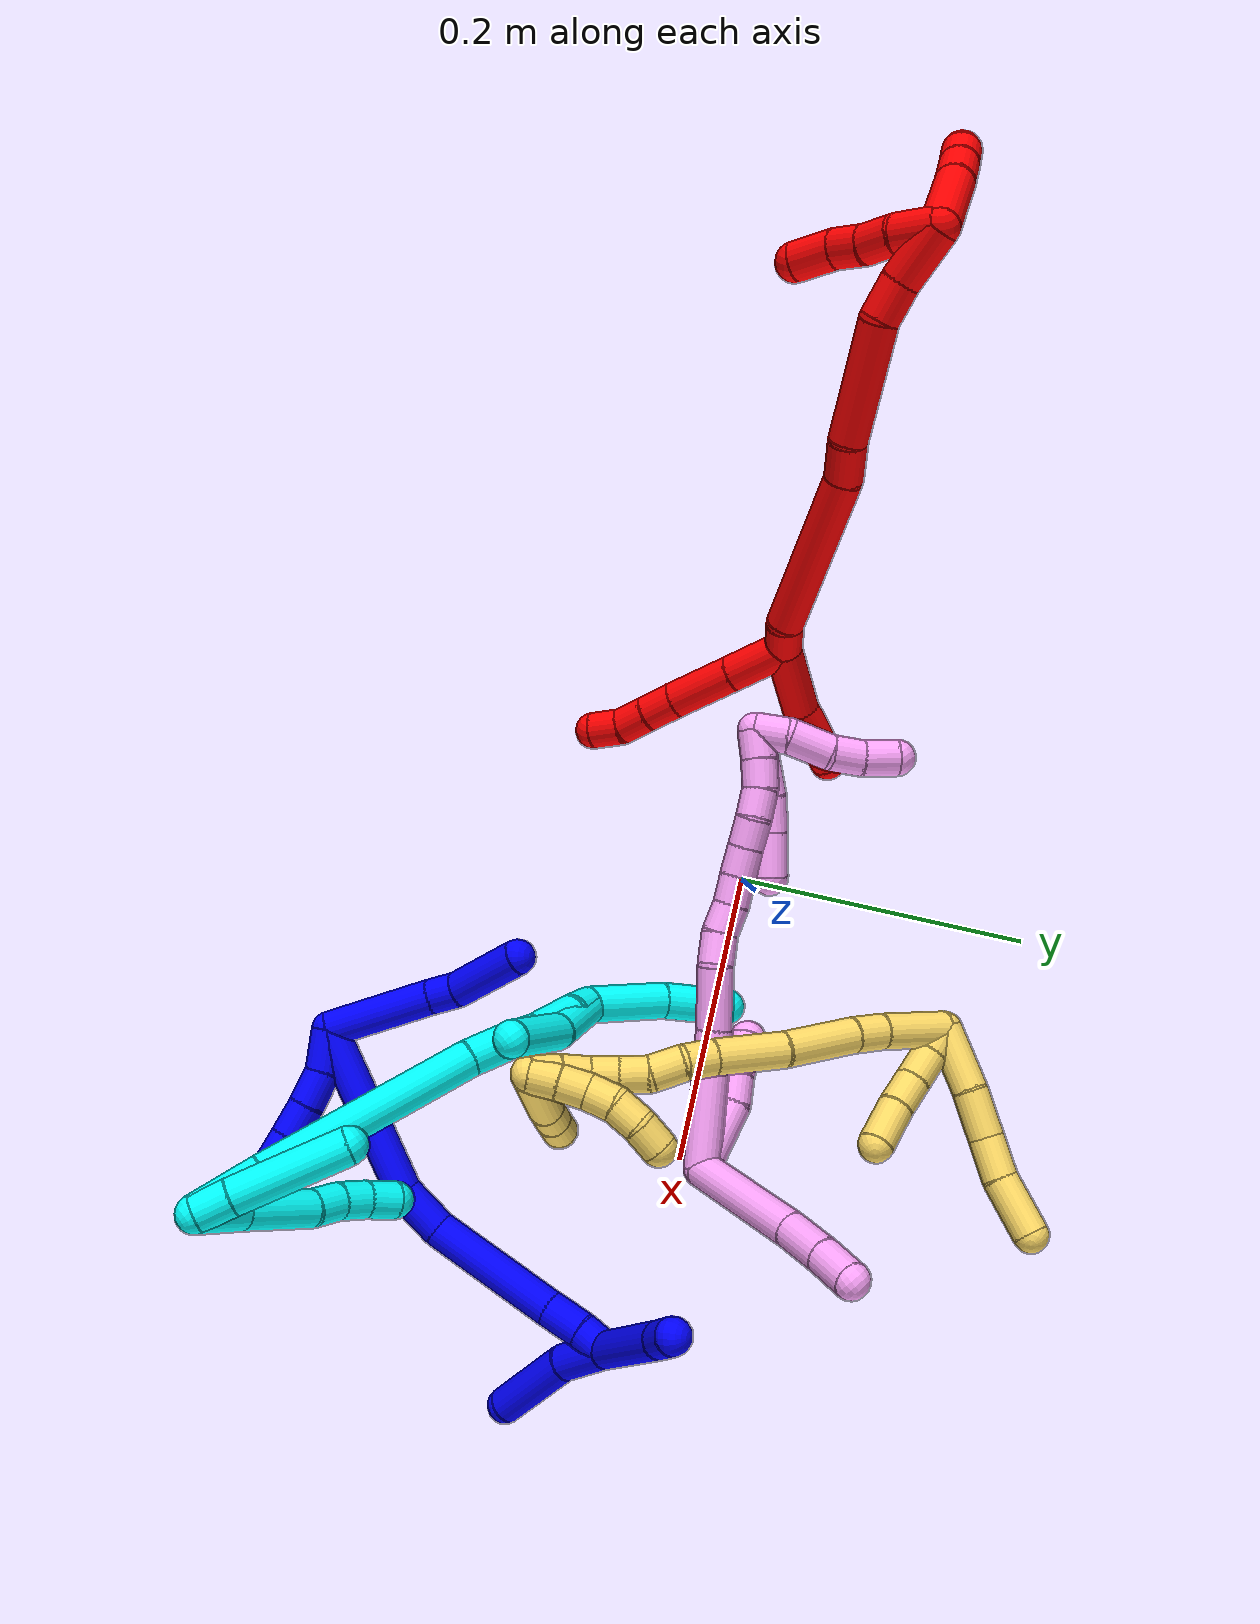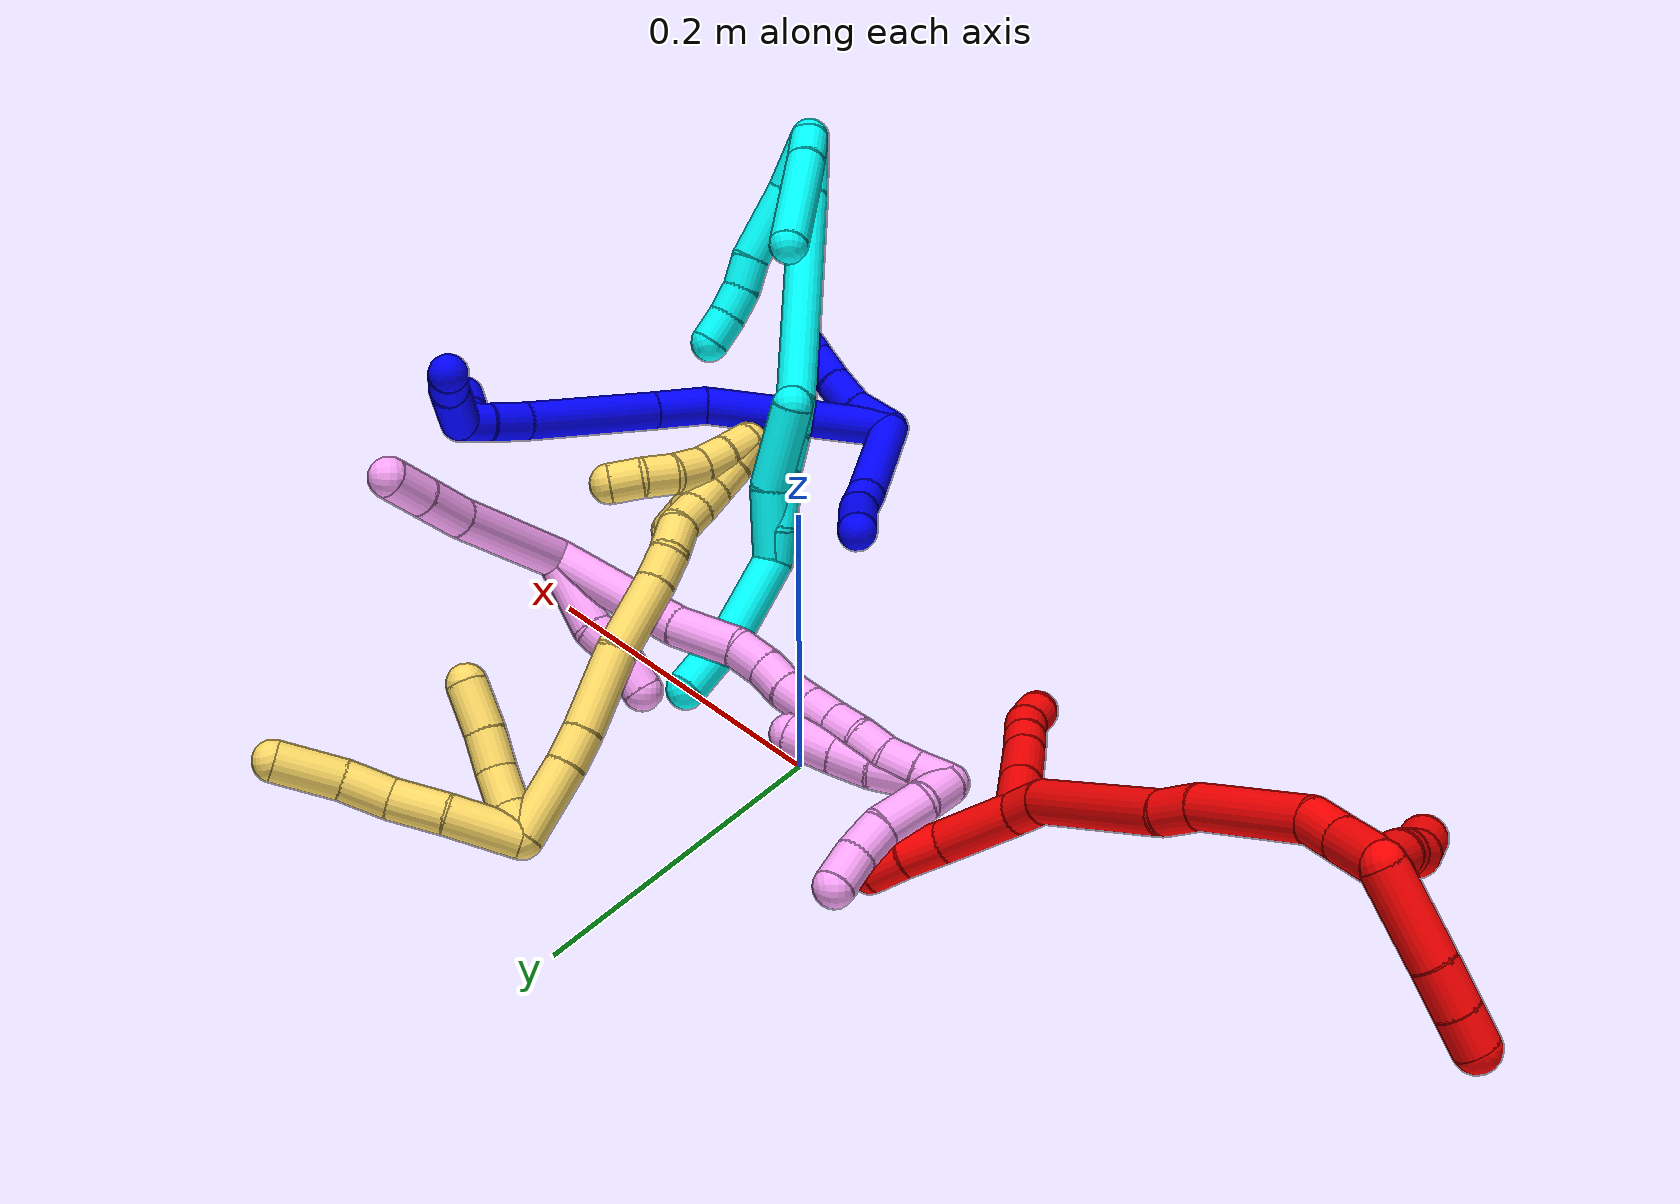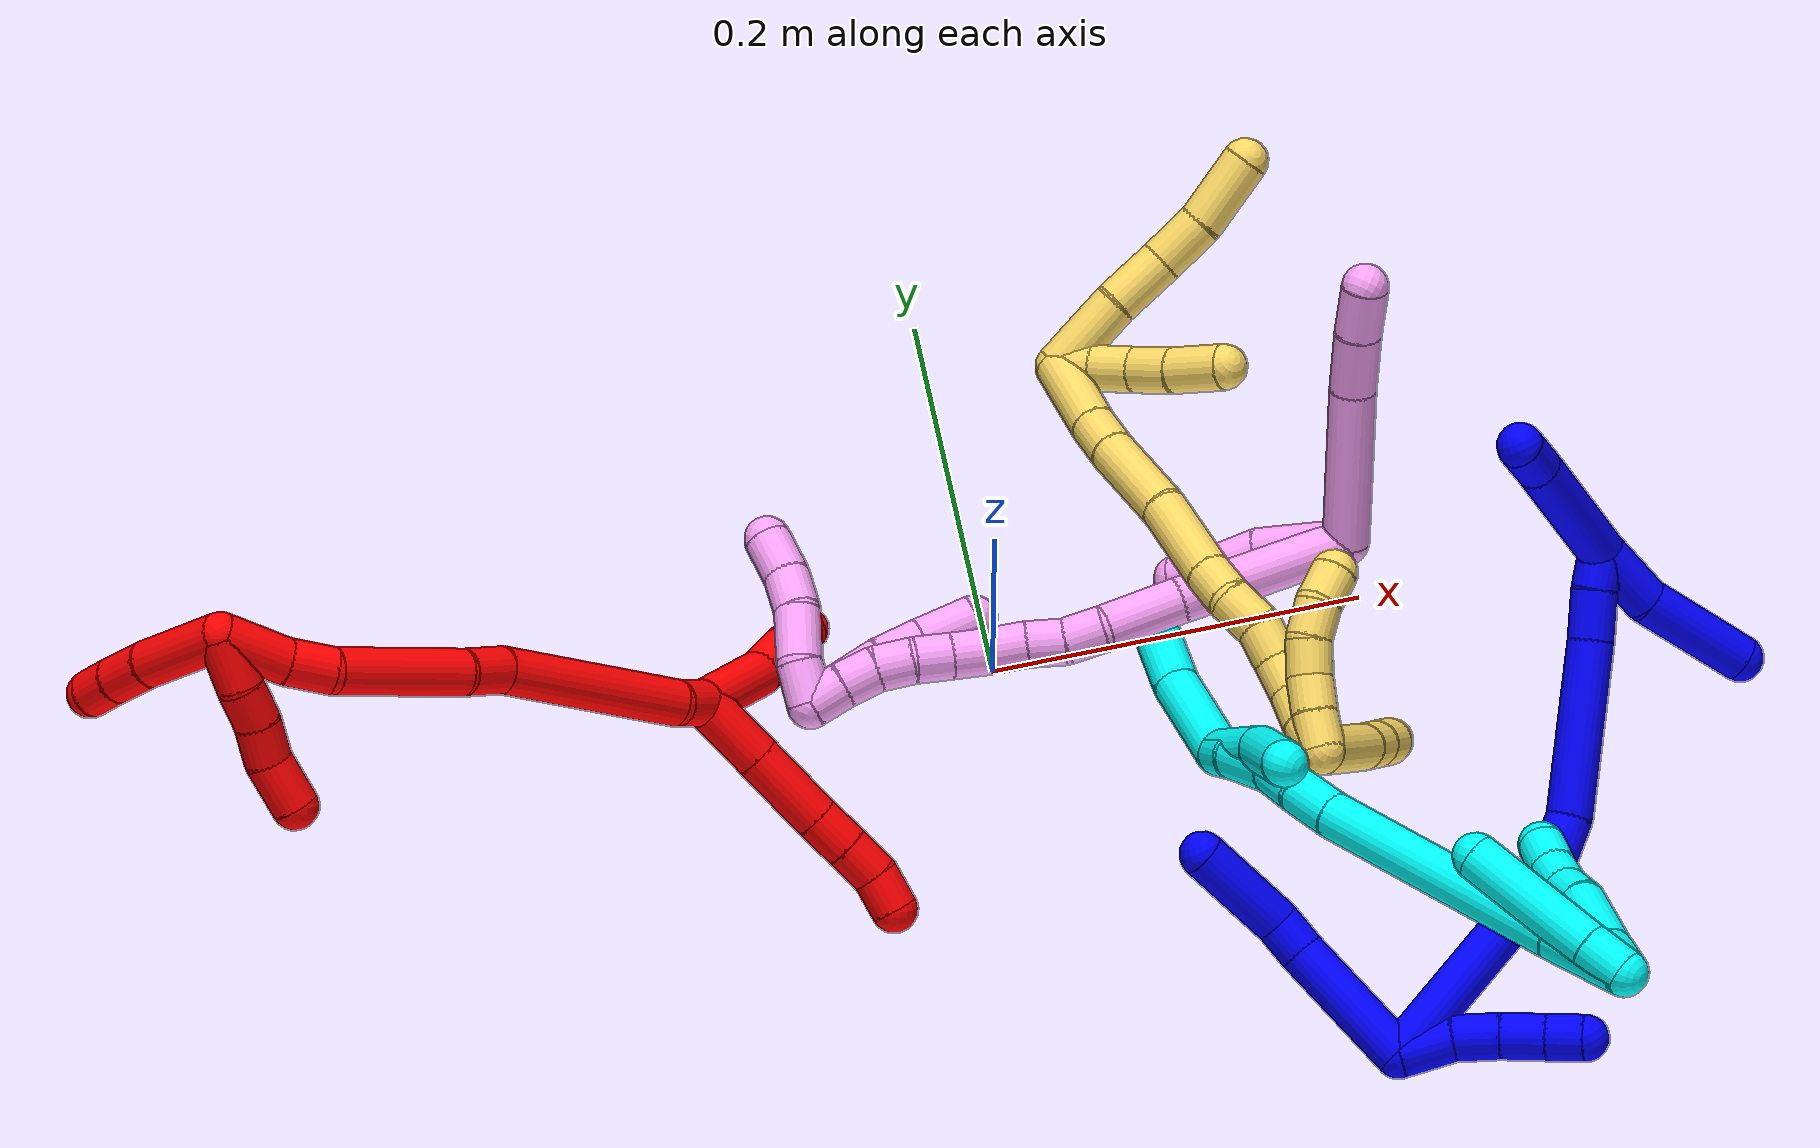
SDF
<sdf version="1.7">
 <world name="default">
  <plugin name="TubeGeneratorPlugin" filename="libtube_generator_plugin.so"/>
  <model name="photoneo_s_sensor">
   <static>1</static>
   <pose>0 0 2 1.57079 1.57079 3.14159</pose>
   <link name="link">
    <inertial><mass>0.1</mass></inertial>
    <sensor name="sensor" type="depth">
     <update_rate>30</update_rate>
     <camera>
      <horizontal_fov>1.22</horizontal_fov>
      <image><width>1920</width><height>1200</height><format>B8G8R8</format></image>
      <clip><near>0.1</near><far>4</far></clip>
      <depth_camera><output>points</output></depth_camera>
     </camera>
     <plugin name="camera_plugin" filename="libgazebo_ros_depth_camera.so">
      <baseline>0.2</baseline>
      <alwaysOn>1</alwaysOn>
      <updateRate>0.0</updateRate>
      <cameraName>camera_ir</cameraName>
      <imageTopicName>/camera/color/image_raw</imageTopicName>
      <cameraInfoTopicName>/camera/color/camera_info</cameraInfoTopicName>
      <depthImageTopicName>/camera/depth/image_raw</depthImageTopicName>
      <depthImageCameraInfoTopicName>/camera/depth/camera_info</depthImageCameraInfoTopicName>
      <pointCloudTopicName>/camera/depth/points</pointCloudTopicName>
      <frameName>fr_optical</frameName>
      <pointCloudCutoff>0.1</pointCloudCutoff>
      <pointCloudCutoffMax>2.0</pointCloudCutoffMax>
      <distortionK1>0</distortionK1>
      <distortionK2>0</distortionK2>
      <distortionK3>0</distortionK3>
      <distortionT1>0</distortionT1>
      <distortionT2>0</distortionT2>
      <CxPrime>0</CxPrime>
      <Cx>0</Cx>
      <Cy>0</Cy>
      <focalLength>0</focalLength>
      <hackBaseline>0</hackBaseline>
     </plugin>
    </sensor>
   </link>
  </model>
  <gravity>0 0 -9.8</gravity>
  <magnetic_field>6e-06 2.3e-05 -4.2e-05</magnetic_field>
  <atmosphere type="adiabatic"/>
  <physics name="default_physics" default="0" type="ode">
   <max_step_size>0.003</max_step_size>
   <real_time_factor>1</real_time_factor>
   <real_time_update_rate>1000</real_time_update_rate>
   <max_contacts>10000</max_contacts>
   <ode>
    <solver>
     <type>quick</type>
     <iters>100</iters>
     <sor>1.3</sor>
     <use_dynamic_moi_rescaling>0</use_dynamic_moi_rescaling>
    </solver>
    <constraints>
     <contact_max_correcting_vel>0</contact_max_correcting_vel>
     <contact_surface_layer>0.001</contact_surface_layer>
     <cfm>0</cfm>
     <erp>0.2</erp>
    </constraints>
   </ode>
  </physics>
  <scene><ambient>0.4 0.4 0.4 1</ambient><background>0.7 0.7 0.7 1</background><shadows>0</shadows></scene>
  <audio><device>default</device></audio>
  <spherical_coordinates>
   <surface_model>EARTH_WGS84</surface_model>
   <latitude_deg>0</latitude_deg>
   <longitude_deg>0</longitude_deg>
   <elevation>0</elevation>
   <heading_deg>0</heading_deg>
  </spherical_coordinates>
  <model name="bin">
   <static>1</static>
   <link name="bottom">
    <collision name="collision-bottom">
     <pose>0 0 -0.01 0 -0 0</pose>
     <geometry><box><size>0.8 0.6 0.02</size></box></geometry>
     <surface>
      <friction><ode><mu>100</mu><mu2>100</mu2></ode></friction>
      <contact><collide_bitmask>65535</collide_bitmask></contact>
     </surface>
    </collision>
   </link>
   <link name="west_wall">
    <collision name="collision-west_wall">
     <pose>-0.41 0 0.1 0 -0 0</pose>
     <geometry><box><size>0.02 0.6 0.2</size></box></geometry>
     <surface>
      <friction><ode><mu>100</mu><mu2>100</mu2></ode></friction>
      <contact><collide_bitmask>65535</collide_bitmask></contact>
     </surface>
    </collision>
   </link>
   <link name="east_wall">
    <collision name="collision-east_wall">
     <pose>0.41 0 0.1 0 -0 0</pose>
     <geometry><box><size>0.02 0.6 0.2</size></box></geometry>
     <surface>
      <friction><ode><mu>100</mu><mu2>100</mu2></ode></friction>
      <contact><collide_bitmask>65535</collide_bitmask></contact>
     </surface>
    </collision>
   </link>
   <link name="south_wall">
    <collision name="collision-south_wall">
     <pose>0 -0.31 0.1 0 -0 0</pose>
     <geometry><box><size>0.8 0.02 0.2</size></box></geometry>
     <surface>
      <friction><ode><mu>100</mu><mu2>100</mu2></ode></friction>
      <contact><collide_bitmask>65535</collide_bitmask></contact>
     </surface>
    </collision>
   </link>
   <link name="north_wall">
    <collision name="collision-north_wall">
     <pose>0 0.31 0.1 0 -0 0</pose>
     <geometry><box><size>0.8 0.02 0.2</size></box></geometry>
     <surface>
      <friction><ode><mu>100</mu><mu2>100</mu2></ode></friction>
      <contact><collide_bitmask>65535</collide_bitmask></contact>
     </surface>
    </collision>
   </link>
  </model>
  <model name="1">
   <static>0</static>
   <link name="1">
    <collision name="collision-cylinder-e_1_2_8">
     <pose>0.017399 0.005508 -0.032552 -2.97398 0.485023 -2.48688</pose>
     <geometry><cylinder><radius>0.0125</radius><length>0.074638</length></cylinder></geometry>
     <surface>
      <friction><ode><mu>1.16</mu><mu2>1.16</mu2><slip1>0</slip1><slip2>0</slip2></ode></friction>
      <contact><ode><kp>1e+06</kp><kd>1</kd><max_vel>0</max_vel><min_depth>0.001</min_depth></ode></contact>
     </surface>
    </collision>
    <visual name="visual-cylinder-e_1_2_8">
     <pose>0.017399 0.005508 -0.032552 -2.97398 0.485023 -2.48688</pose>
     <geometry><cylinder><radius>0.0125</radius><length>0.074638</length></cylinder></geometry>
     <material><ambient>0 0 1 1</ambient></material>
    </visual>
    <collision name="collision-cylinder-e_2_8_9">
     <pose>0.03836 0.011731 -0.074585 -3.06633 0.358412 -2.73175</pose>
     <geometry><cylinder><radius>0.0125</radius><length>0.020306</length></cylinder></geometry>
     <surface>
      <friction><ode><mu>1.16</mu><mu2>1.16</mu2><slip1>0</slip1><slip2>0</slip2></ode></friction>
      <contact><ode><kp>1e+06</kp><kd>1</kd><max_vel>0</max_vel><min_depth>0.001</min_depth></ode></contact>
     </surface>
    </collision>
    <visual name="visual-cylinder-e_2_8_9">
     <pose>0.03836 0.011731 -0.074585 -3.06633 0.358412 -2.73175</pose>
     <geometry><cylinder><radius>0.0125</radius><length>0.020306</length></cylinder></geometry>
     <material><ambient>0 0 1 1</ambient></material>
    </visual>
    <collision name="collision-cylinder-e_3_9_6">
     <pose>0.049936 0.005338 -0.109424 2.86833 0.295435 1.64979</pose>
     <geometry><cylinder><radius>0.0125</radius><length>0.055056</length></cylinder></geometry>
     <surface>
      <friction><ode><mu>1.16</mu><mu2>1.16</mu2><slip1>0</slip1><slip2>0</slip2></ode></friction>
      <contact><ode><kp>1e+06</kp><kd>1</kd><max_vel>0</max_vel><min_depth>0.001</min_depth></ode></contact>
     </surface>
    </collision>
    <visual name="visual-cylinder-e_3_9_6">
     <pose>0.049936 0.005338 -0.109424 2.86833 0.295435 1.64979</pose>
     <geometry><cylinder><radius>0.0125</radius><length>0.055056</length></cylinder></geometry>
     <material><ambient>0 0 1 1</ambient></material>
    </visual>
    <collision name="collision-cylinder-e_1_2_10">
     <pose>-0.012577 0.007822 0.001951 -1.32632 -1.00079 0.807398</pose>
     <geometry><cylinder><radius>0.0125</radius><length>0.029877</length></cylinder></geometry>
     <surface>
      <friction><ode><mu>1.16</mu><mu2>1.16</mu2><slip1>0</slip1><slip2>0</slip2></ode></friction>
      <contact><ode><kp>1e+06</kp><kd>1</kd><max_vel>0</max_vel><min_depth>0.001</min_depth></ode></contact>
     </surface>
    </collision>
    <visual name="visual-cylinder-e_1_2_10">
     <pose>-0.012577 0.007822 0.001951 -1.32632 -1.00079 0.807398</pose>
     <geometry><cylinder><radius>0.0125</radius><length>0.029877</length></cylinder></geometry>
     <material><ambient>0 0 1 1</ambient></material>
    </visual>
    <collision name="collision-cylinder-e_2_10_11">
     <pose>-0.036754 0.019194 0.007849 -0.732612 -1.14163 0.483042</pose>
     <geometry><cylinder><radius>0.0125</radius><length>0.025515</length></cylinder></geometry>
     <surface>
      <friction><ode><mu>1.16</mu><mu2>1.16</mu2><slip1>0</slip1><slip2>0</slip2></ode></friction>
      <contact><ode><kp>1e+06</kp><kd>1</kd><max_vel>0</max_vel><min_depth>0.001</min_depth></ode></contact>
     </surface>
    </collision>
    <visual name="visual-cylinder-e_2_10_11">
     <pose>-0.036754 0.019194 0.007849 -0.732612 -1.14163 0.483042</pose>
     <geometry><cylinder><radius>0.0125</radius><length>0.025515</length></cylinder></geometry>
     <material><ambient>0 0 1 1</ambient></material>
    </visual>
    <collision name="collision-cylinder-e_3_11_12">
     <pose>-0.059288 0.025647 0.016328 -0.569625 -1.11339 0.360462</pose>
     <geometry><cylinder><radius>0.0125</radius><length>0.024374</length></cylinder></geometry>
     <surface>
      <friction><ode><mu>1.16</mu><mu2>1.16</mu2><slip1>0</slip1><slip2>0</slip2></ode></friction>
      <contact><ode><kp>1e+06</kp><kd>1</kd><max_vel>0</max_vel><min_depth>0.001</min_depth></ode></contact>
     </surface>
    </collision>
    <visual name="visual-cylinder-e_3_11_12">
     <pose>-0.059288 0.025647 0.016328 -0.569625 -1.11339 0.360462</pose>
     <geometry><cylinder><radius>0.0125</radius><length>0.024374</length></cylinder></geometry>
     <material><ambient>0 0 1 1</ambient></material>
    </visual>
    <collision name="collision-cylinder-e_4_12_5">
     <pose>-0.079464 0.030573 0.024447 -0.513728 -1.15155 0.33777</pose>
     <geometry><cylinder><radius>0.0125</radius><length>0.020234</length></cylinder></geometry>
     <surface>
      <friction><ode><mu>1.16</mu><mu2>1.16</mu2><slip1>0</slip1><slip2>0</slip2></ode></friction>
      <contact><ode><kp>1e+06</kp><kd>1</kd><max_vel>0</max_vel><min_depth>0.001</min_depth></ode></contact>
     </surface>
    </collision>
    <visual name="visual-cylinder-e_4_12_5">
     <pose>-0.079464 0.030573 0.024447 -0.513728 -1.15155 0.33777</pose>
     <geometry><cylinder><radius>0.0125</radius><length>0.020234</length></cylinder></geometry>
     <material><ambient>0 0 1 1</ambient></material>
    </visual>
    <collision name="collision-cylinder-e_1_2_13">
     <pose>-0.037778 0.042914 -0.022683 -2.05703 -0.661359 1.03574</pose>
     <geometry><cylinder><radius>0.0125</radius><length>0.123017</length></cylinder></geometry>
     <surface>
      <friction><ode><mu>1.16</mu><mu2>1.16</mu2><slip1>0</slip1><slip2>0</slip2></ode></friction>
      <contact><ode><kp>1e+06</kp><kd>1</kd><max_vel>0</max_vel><min_depth>0.001</min_depth></ode></contact>
     </surface>
    </collision>
    <visual name="visual-cylinder-e_1_2_13">
     <pose>-0.037778 0.042914 -0.022683 -2.05703 -0.661359 1.03574</pose>
     <geometry><cylinder><radius>0.0125</radius><length>0.123017</length></cylinder></geometry>
     <material><ambient>0 0 1 1</ambient></material>
    </visual>
    <collision name="collision-cylinder-e_2_13_14">
     <pose>-0.082355 0.098085 -0.056064 -2.28839 -0.395854 0.831106</pose>
     <geometry><cylinder><radius>0.0125</radius><length>0.035264</length></cylinder></geometry>
     <surface>
      <friction><ode><mu>1.16</mu><mu2>1.16</mu2><slip1>0</slip1><slip2>0</slip2></ode></friction>
      <contact><ode><kp>1e+06</kp><kd>1</kd><max_vel>0</max_vel><min_depth>0.001</min_depth></ode></contact>
     </surface>
    </collision>
    <visual name="visual-cylinder-e_2_13_14">
     <pose>-0.082355 0.098085 -0.056064 -2.28839 -0.395854 0.831106</pose>
     <geometry><cylinder><radius>0.0125</radius><length>0.035264</length></cylinder></geometry>
     <material><ambient>0 0 1 1</ambient></material>
    </visual>
    <collision name="collision-cylinder-e_3_14_15">
     <pose>-0.103852 0.133269 -0.105343 -2.6054 -0.316493 1.05252</pose>
     <geometry><cylinder><radius>0.0125</radius><length>0.094451</length></cylinder></geometry>
     <surface>
      <friction><ode><mu>1.16</mu><mu2>1.16</mu2><slip1>0</slip1><slip2>0</slip2></ode></friction>
      <contact><ode><kp>1e+06</kp><kd>1</kd><max_vel>0</max_vel><min_depth>0.001</min_depth></ode></contact>
     </surface>
    </collision>
    <visual name="visual-cylinder-e_3_14_15">
     <pose>-0.103852 0.133269 -0.105343 -2.6054 -0.316493 1.05252</pose>
     <geometry><cylinder><radius>0.0125</radius><length>0.094451</length></cylinder></geometry>
     <material><ambient>0 0 1 1</ambient></material>
    </visual>
    <collision name="collision-cylinder-e_4_15_16">
     <pose>-0.122816 0.161552 -0.155616 -2.71205 -0.320282 1.27476</pose>
     <geometry><cylinder><radius>0.0125</radius><length>0.027097</length></cylinder></geometry>
     <surface>
      <friction><ode><mu>1.16</mu><mu2>1.16</mu2><slip1>0</slip1><slip2>0</slip2></ode></friction>
      <contact><ode><kp>1e+06</kp><kd>1</kd><max_vel>0</max_vel><min_depth>0.001</min_depth></ode></contact>
     </surface>
    </collision>
    <visual name="visual-cylinder-e_4_15_16">
     <pose>-0.122816 0.161552 -0.155616 -2.71205 -0.320282 1.27476</pose>
     <geometry><cylinder><radius>0.0125</radius><length>0.027097</length></cylinder></geometry>
     <material><ambient>0 0 1 1</ambient></material>
    </visual>
    <collision name="collision-cylinder-e_5_16_1">
     <pose>-0.13109 0.171568 -0.175302 -2.61375 -0.408805 1.30875</pose>
     <geometry><cylinder><radius>0.0125</radius><length>0.020171</length></cylinder></geometry>
     <surface>
      <friction><ode><mu>1.16</mu><mu2>1.16</mu2><slip1>0</slip1><slip2>0</slip2></ode></friction>
      <contact><ode><kp>1e+06</kp><kd>1</kd><max_vel>0</max_vel><min_depth>0.001</min_depth></ode></contact>
     </surface>
    </collision>
    <visual name="visual-cylinder-e_5_16_1">
     <pose>-0.13109 0.171568 -0.175302 -2.61375 -0.408805 1.30875</pose>
     <geometry><cylinder><radius>0.0125</radius><length>0.020171</length></cylinder></geometry>
     <material><ambient>0 0 1 1</ambient></material>
    </visual>
    <collision name="collision-cylinder-e_1_1_17">
     <pose>-0.139025 0.155519 -0.215409 2.56878 -0.102363 -0.344438</pose>
     <geometry><cylinder><radius>0.0125</radius><length>0.076825</length></cylinder></geometry>
     <surface>
      <friction><ode><mu>1.16</mu><mu2>1.16</mu2><slip1>0</slip1><slip2>0</slip2></ode></friction>
      <contact><ode><kp>1e+06</kp><kd>1</kd><max_vel>0</max_vel><min_depth>0.001</min_depth></ode></contact>
     </surface>
    </collision>
    <visual name="visual-cylinder-e_1_1_17">
     <pose>-0.139025 0.155519 -0.215409 2.56878 -0.102363 -0.344438</pose>
     <geometry><cylinder><radius>0.0125</radius><length>0.076825</length></cylinder></geometry>
     <material><ambient>0 0 1 1</ambient></material>
    </visual>
    <collision name="collision-cylinder-e_2_17_4">
     <pose>-0.144708 0.127451 -0.256299 2.44403 -0.152292 -0.413604</pose>
     <geometry><cylinder><radius>0.0125</radius><length>0.023175</length></cylinder></geometry>
     <surface>
      <friction><ode><mu>1.16</mu><mu2>1.16</mu2><slip1>0</slip1><slip2>0</slip2></ode></friction>
      <contact><ode><kp>1e+06</kp><kd>1</kd><max_vel>0</max_vel><min_depth>0.001</min_depth></ode></contact>
     </surface>
    </collision>
    <visual name="visual-cylinder-e_2_17_4">
     <pose>-0.144708 0.127451 -0.256299 2.44403 -0.152292 -0.413604</pose>
     <geometry><cylinder><radius>0.0125</radius><length>0.023175</length></cylinder></geometry>
     <material><ambient>0 0 1 1</ambient></material>
    </visual>
    <collision name="collision-cylinder-e_1_1_18">
     <pose>-0.13863 0.181469 -0.165689 -0.289247 -0.189856 0.027732</pose>
     <geometry><cylinder><radius>0.0125</radius><length>0.037414</length></cylinder></geometry>
     <surface>
      <friction><ode><mu>1.16</mu><mu2>1.16</mu2><slip1>0</slip1><slip2>0</slip2></ode></friction>
      <contact><ode><kp>1e+06</kp><kd>1</kd><max_vel>0</max_vel><min_depth>0.001</min_depth></ode></contact>
     </surface>
    </collision>
    <visual name="visual-cylinder-e_1_1_18">
     <pose>-0.13863 0.181469 -0.165689 -0.289247 -0.189856 0.027732</pose>
     <geometry><cylinder><radius>0.0125</radius><length>0.037414</length></cylinder></geometry>
     <material><ambient>0 0 1 1</ambient></material>
    </visual>
    <collision name="collision-cylinder-e_2_18_3">
     <pose>-0.154189 0.199432 -0.122145 -0.456026 -0.394551 0.092695</pose>
     <geometry><cylinder><radius>0.0125</radius><length>0.062586</length></cylinder></geometry>
     <surface>
      <friction><ode><mu>1.16</mu><mu2>1.16</mu2><slip1>0</slip1><slip2>0</slip2></ode></friction>
      <contact><ode><kp>1e+06</kp><kd>1</kd><max_vel>0</max_vel><min_depth>0.001</min_depth></ode></contact>
     </surface>
    </collision>
    <visual name="visual-cylinder-e_2_18_3">
     <pose>-0.154189 0.199432 -0.122145 -0.456026 -0.394551 0.092695</pose>
     <geometry><cylinder><radius>0.0125</radius><length>0.062586</length></cylinder></geometry>
     <material><ambient>0 0 1 1</ambient></material>
    </visual>
    <collision name="collision-sphere-3">
     <pose>-0.166218 0.212154 -0.096208 0 -0 0</pose>
     <geometry><sphere><radius>0.0125</radius></sphere></geometry>
     <surface>
      <friction><ode><mu>1.16</mu><mu2>1.16</mu2><slip1>0</slip1><slip2>0</slip2></ode></friction>
      <contact><ode><kp>1e+06</kp><kd>1</kd><max_vel>0</max_vel><min_depth>0.001</min_depth></ode></contact>
     </surface>
    </collision>
    <visual name="visual-sphere-3">
     <pose>-0.166218 0.212154 -0.096208 0 -0 0</pose>
     <geometry><sphere><radius>0.0125</radius></sphere></geometry>
     <material><ambient>0 0 1 1</ambient></material>
    </visual>
    <collision name="collision-sphere-11">
     <pose>-0.048354 0.022744 0.011795 0 -0 0</pose>
     <geometry><sphere><radius>0.0125</radius></sphere></geometry>
     <surface>
      <friction><ode><mu>1.16</mu><mu2>1.16</mu2><slip1>0</slip1><slip2>0</slip2></ode></friction>
      <contact><ode><kp>1e+06</kp><kd>1</kd><max_vel>0</max_vel><min_depth>0.001</min_depth></ode></contact>
     </surface>
    </collision>
    <visual name="visual-sphere-11">
     <pose>-0.048354 0.022744 0.011795 0 -0 0</pose>
     <geometry><sphere><radius>0.0125</radius></sphere></geometry>
     <material><ambient>0 0 1 1</ambient></material>
    </visual>
    <collision name="collision-sphere-10">
     <pose>-0.025153 0.015643 0.003903 0 -0 0</pose>
     <geometry><sphere><radius>0.0125</radius></sphere></geometry>
     <surface>
      <friction><ode><mu>1.16</mu><mu2>1.16</mu2><slip1>0</slip1><slip2>0</slip2></ode></friction>
      <contact><ode><kp>1e+06</kp><kd>1</kd><max_vel>0</max_vel><min_depth>0.001</min_depth></ode></contact>
     </surface>
    </collision>
    <visual name="visual-sphere-10">
     <pose>-0.025153 0.015643 0.003903 0 -0 0</pose>
     <geometry><sphere><radius>0.0125</radius></sphere></geometry>
     <material><ambient>0 0 1 1</ambient></material>
    </visual>
    <collision name="collision-sphere-6">
     <pose>0.057951 -0.001769 -0.134782 0 -0 0</pose>
     <geometry><sphere><radius>0.0125</radius></sphere></geometry>
     <surface>
      <friction><ode><mu>1.16</mu><mu2>1.16</mu2><slip1>0</slip1><slip2>0</slip2></ode></friction>
      <contact><ode><kp>1e+06</kp><kd>1</kd><max_vel>0</max_vel><min_depth>0.001</min_depth></ode></contact>
     </surface>
    </collision>
    <visual name="visual-sphere-6">
     <pose>0.057951 -0.001769 -0.134782 0 -0 0</pose>
     <geometry><sphere><radius>0.0125</radius></sphere></geometry>
     <material><ambient>0 0 1 1</ambient></material>
    </visual>
    <collision name="collision-sphere-9">
     <pose>0.041921 0.012446 -0.084066 0 -0 0</pose>
     <geometry><sphere><radius>0.0125</radius></sphere></geometry>
     <surface>
      <friction><ode><mu>1.16</mu><mu2>1.16</mu2><slip1>0</slip1><slip2>0</slip2></ode></friction>
      <contact><ode><kp>1e+06</kp><kd>1</kd><max_vel>0</max_vel><min_depth>0.001</min_depth></ode></contact>
     </surface>
    </collision>
    <visual name="visual-sphere-9">
     <pose>0.041921 0.012446 -0.084066 0 -0 0</pose>
     <geometry><sphere><radius>0.0125</radius></sphere></geometry>
     <material><ambient>0 0 1 1</ambient></material>
    </visual>
    <collision name="collision-sphere-2">
     <geometry><sphere><radius>0.0125</radius></sphere></geometry>
     <surface>
      <friction><ode><mu>1.16</mu><mu2>1.16</mu2><slip1>0</slip1><slip2>0</slip2></ode></friction>
      <contact><ode><kp>1e+06</kp><kd>1</kd><max_vel>0</max_vel><min_depth>0.001</min_depth></ode></contact>
     </surface>
    </collision>
    <visual name="visual-sphere-2">
     <geometry><sphere><radius>0.0125</radius></sphere></geometry>
     <material><ambient>0 0 1 1</ambient></material>
    </visual>
    <collision name="collision-sphere-8">
     <pose>0.034798 0.011016 -0.065104 0 -0 0</pose>
     <geometry><sphere><radius>0.0125</radius></sphere></geometry>
     <surface>
      <friction><ode><mu>1.16</mu><mu2>1.16</mu2><slip1>0</slip1><slip2>0</slip2></ode></friction>
      <contact><ode><kp>1e+06</kp><kd>1</kd><max_vel>0</max_vel><min_depth>0.001</min_depth></ode></contact>
     </surface>
    </collision>
    <visual name="visual-sphere-8">
     <pose>0.034798 0.011016 -0.065104 0 -0 0</pose>
     <geometry><sphere><radius>0.0125</radius></sphere></geometry>
     <material><ambient>0 0 1 1</ambient></material>
    </visual>
    <collision name="collision-sphere-12">
     <pose>-0.070223 0.028549 0.02086 0 -0 0</pose>
     <geometry><sphere><radius>0.0125</radius></sphere></geometry>
     <surface>
      <friction><ode><mu>1.16</mu><mu2>1.16</mu2><slip1>0</slip1><slip2>0</slip2></ode></friction>
      <contact><ode><kp>1e+06</kp><kd>1</kd><max_vel>0</max_vel><min_depth>0.001</min_depth></ode></contact>
     </surface>
    </collision>
    <visual name="visual-sphere-12">
     <pose>-0.070223 0.028549 0.02086 0 -0 0</pose>
     <geometry><sphere><radius>0.0125</radius></sphere></geometry>
     <material><ambient>0 0 1 1</ambient></material>
    </visual>
    <collision name="collision-sphere-5">
     <pose>-0.088705 0.032597 0.028034 0 -0 0</pose>
     <geometry><sphere><radius>0.0125</radius></sphere></geometry>
     <surface>
      <friction><ode><mu>1.16</mu><mu2>1.16</mu2><slip1>0</slip1><slip2>0</slip2></ode></friction>
      <contact><ode><kp>1e+06</kp><kd>1</kd><max_vel>0</max_vel><min_depth>0.001</min_depth></ode></contact>
     </surface>
    </collision>
    <visual name="visual-sphere-5">
     <pose>-0.088705 0.032597 0.028034 0 -0 0</pose>
     <geometry><sphere><radius>0.0125</radius></sphere></geometry>
     <material><ambient>0 0 1 1</ambient></material>
    </visual>
    <collision name="collision-sphere-13">
     <pose>-0.075556 0.085828 -0.045366 0 -0 0</pose>
     <geometry><sphere><radius>0.0125</radius></sphere></geometry>
     <surface>
      <friction><ode><mu>1.16</mu><mu2>1.16</mu2><slip1>0</slip1><slip2>0</slip2></ode></friction>
      <contact><ode><kp>1e+06</kp><kd>1</kd><max_vel>0</max_vel><min_depth>0.001</min_depth></ode></contact>
     </surface>
    </collision>
    <visual name="visual-sphere-13">
     <pose>-0.075556 0.085828 -0.045366 0 -0 0</pose>
     <geometry><sphere><radius>0.0125</radius></sphere></geometry>
     <material><ambient>0 0 1 1</ambient></material>
    </visual>
    <collision name="collision-sphere-14">
     <pose>-0.089154 0.110342 -0.066762 0 -0 0</pose>
     <geometry><sphere><radius>0.0125</radius></sphere></geometry>
     <surface>
      <friction><ode><mu>1.16</mu><mu2>1.16</mu2><slip1>0</slip1><slip2>0</slip2></ode></friction>
      <contact><ode><kp>1e+06</kp><kd>1</kd><max_vel>0</max_vel><min_depth>0.001</min_depth></ode></contact>
     </surface>
    </collision>
    <visual name="visual-sphere-14">
     <pose>-0.089154 0.110342 -0.066762 0 -0 0</pose>
     <geometry><sphere><radius>0.0125</radius></sphere></geometry>
     <material><ambient>0 0 1 1</ambient></material>
    </visual>
    <collision name="collision-sphere-15">
     <pose>-0.11855 0.156197 -0.143924 0 -0 0</pose>
     <geometry><sphere><radius>0.0125</radius></sphere></geometry>
     <surface>
      <friction><ode><mu>1.16</mu><mu2>1.16</mu2><slip1>0</slip1><slip2>0</slip2></ode></friction>
      <contact><ode><kp>1e+06</kp><kd>1</kd><max_vel>0</max_vel><min_depth>0.001</min_depth></ode></contact>
     </surface>
    </collision>
    <visual name="visual-sphere-15">
     <pose>-0.11855 0.156197 -0.143924 0 -0 0</pose>
     <geometry><sphere><radius>0.0125</radius></sphere></geometry>
     <material><ambient>0 0 1 1</ambient></material>
    </visual>
    <collision name="collision-sphere-16">
     <pose>-0.127081 0.166907 -0.167307 0 -0 0</pose>
     <geometry><sphere><radius>0.0125</radius></sphere></geometry>
     <surface>
      <friction><ode><mu>1.16</mu><mu2>1.16</mu2><slip1>0</slip1><slip2>0</slip2></ode></friction>
      <contact><ode><kp>1e+06</kp><kd>1</kd><max_vel>0</max_vel><min_depth>0.001</min_depth></ode></contact>
     </surface>
    </collision>
    <visual name="visual-sphere-16">
     <pose>-0.127081 0.166907 -0.167307 0 -0 0</pose>
     <geometry><sphere><radius>0.0125</radius></sphere></geometry>
     <material><ambient>0 0 1 1</ambient></material>
    </visual>
    <collision name="collision-sphere-1">
     <pose>-0.135099 0.17623 -0.183296 0 -0 0</pose>
     <geometry><sphere><radius>0.0125</radius></sphere></geometry>
     <surface>
      <friction><ode><mu>1.16</mu><mu2>1.16</mu2><slip1>0</slip1><slip2>0</slip2></ode></friction>
      <contact><ode><kp>1e+06</kp><kd>1</kd><max_vel>0</max_vel><min_depth>0.001</min_depth></ode></contact>
     </surface>
    </collision>
    <visual name="visual-sphere-1">
     <pose>-0.135099 0.17623 -0.183296 0 -0 0</pose>
     <geometry><sphere><radius>0.0125</radius></sphere></geometry>
     <material><ambient>0 0 1 1</ambient></material>
    </visual>
    <collision name="collision-sphere-18">
     <pose>-0.14216 0.186709 -0.148081 0 -0 0</pose>
     <geometry><sphere><radius>0.0125</radius></sphere></geometry>
     <surface>
      <friction><ode><mu>1.16</mu><mu2>1.16</mu2><slip1>0</slip1><slip2>0</slip2></ode></friction>
      <contact><ode><kp>1e+06</kp><kd>1</kd><max_vel>0</max_vel><min_depth>0.001</min_depth></ode></contact>
     </surface>
    </collision>
    <visual name="visual-sphere-18">
     <pose>-0.14216 0.186709 -0.148081 0 -0 0</pose>
     <geometry><sphere><radius>0.0125</radius></sphere></geometry>
     <material><ambient>0 0 1 1</ambient></material>
    </visual>
    <collision name="collision-sphere-17">
     <pose>-0.14295 0.134808 -0.247521 0 -0 0</pose>
     <geometry><sphere><radius>0.0125</radius></sphere></geometry>
     <surface>
      <friction><ode><mu>1.16</mu><mu2>1.16</mu2><slip1>0</slip1><slip2>0</slip2></ode></friction>
      <contact><ode><kp>1e+06</kp><kd>1</kd><max_vel>0</max_vel><min_depth>0.001</min_depth></ode></contact>
     </surface>
    </collision>
    <visual name="visual-sphere-17">
     <pose>-0.14295 0.134808 -0.247521 0 -0 0</pose>
     <geometry><sphere><radius>0.0125</radius></sphere></geometry>
     <material><ambient>0 0 1 1</ambient></material>
    </visual>
    <collision name="collision-sphere-4">
     <pose>-0.146465 0.120095 -0.265077 0 -0 0</pose>
     <geometry><sphere><radius>0.0125</radius></sphere></geometry>
     <surface>
      <friction><ode><mu>1.16</mu><mu2>1.16</mu2><slip1>0</slip1><slip2>0</slip2></ode></friction>
      <contact><ode><kp>1e+06</kp><kd>1</kd><max_vel>0</max_vel><min_depth>0.001</min_depth></ode></contact>
     </surface>
    </collision>
    <visual name="visual-sphere-4">
     <pose>-0.146465 0.120095 -0.265077 0 -0 0</pose>
     <geometry><sphere><radius>0.0125</radius></sphere></geometry>
     <material><ambient>0 0 1 1</ambient></material>
    </visual>
    <inertial>
     <pose>-0.068991 0.088329 -0.090159 0 -0 0</pose>
     <mass>0.75</mass>
     <inertia>
      <ixx>0.00029</ixx>
      <ixy>0</ixy>
      <ixz>0</ixz>
      <iyy>0.000227</iyy>
      <iyz>0</iyz>
      <izz>-4.3e-05</izz>
     </inertia>
    </inertial>
   </link>
   <pose>0.162112 -0.256987 0.012392 -2.22549 0.615618 3.00043</pose>
  </model>
  <model name="2">
   <static>0</static>
   <link name="2">
    <collision name="collision-cylinder-e_1_2_8">
     <pose>0.009675 -0.014871 -0.009185 2.1241 0.50552 0.867405</pose>
     <geometry><cylinder><radius>0.0125</radius><length>0.039956</length></cylinder></geometry>
     <surface>
      <friction><ode><mu>1.16</mu><mu2>1.16</mu2><slip1>0</slip1><slip2>0</slip2></ode></friction>
      <contact><ode><kp>1e+06</kp><kd>1</kd><max_vel>0</max_vel><min_depth>0.001</min_depth></ode></contact>
     </surface>
    </collision>
    <visual name="visual-cylinder-e_1_2_8">
     <pose>0.009675 -0.014871 -0.009185 2.1241 0.50552 0.867405</pose>
     <geometry><cylinder><radius>0.0125</radius><length>0.039956</length></cylinder></geometry>
     <material><ambient>1 0 0 1</ambient></material>
    </visual>
    <collision name="collision-cylinder-e_2_8_9">
     <pose>0.030264 -0.046567 -0.028665 2.11989 0.505426 0.863497</pose>
     <geometry><cylinder><radius>0.0125</radius><length>0.045086</length></cylinder></geometry>
     <surface>
      <friction><ode><mu>1.16</mu><mu2>1.16</mu2><slip1>0</slip1><slip2>0</slip2></ode></friction>
      <contact><ode><kp>1e+06</kp><kd>1</kd><max_vel>0</max_vel><min_depth>0.001</min_depth></ode></contact>
     </surface>
    </collision>
    <visual name="visual-cylinder-e_2_8_9">
     <pose>0.030264 -0.046567 -0.028665 2.11989 0.505426 0.863497</pose>
     <geometry><cylinder><radius>0.0125</radius><length>0.045086</length></cylinder></geometry>
     <material><ambient>1 0 0 1</ambient></material>
    </visual>
    <collision name="collision-cylinder-e_3_9_10">
     <pose>0.046957 -0.071424 -0.044038 2.13464 0.546286 0.940991</pose>
     <geometry><cylinder><radius>0.0125</radius><length>0.022242</length></cylinder></geometry>
     <surface>
      <friction><ode><mu>1.16</mu><mu2>1.16</mu2><slip1>0</slip1><slip2>0</slip2></ode></friction>
      <contact><ode><kp>1e+06</kp><kd>1</kd><max_vel>0</max_vel><min_depth>0.001</min_depth></ode></contact>
     </surface>
    </collision>
    <visual name="visual-cylinder-e_3_9_10">
     <pose>0.046957 -0.071424 -0.044038 2.13464 0.546286 0.940991</pose>
     <geometry><cylinder><radius>0.0125</radius><length>0.022242</length></cylinder></geometry>
     <material><ambient>1 0 0 1</ambient></material>
    </visual>
    <collision name="collision-cylinder-e_4_10_11">
     <pose>0.057978 -0.08731 -0.054242 2.14893 0.509791 0.896898</pose>
     <geometry><cylinder><radius>0.0125</radius><length>0.021489</length></cylinder></geometry>
     <surface>
      <friction><ode><mu>1.16</mu><mu2>1.16</mu2><slip1>0</slip1><slip2>0</slip2></ode></friction>
      <contact><ode><kp>1e+06</kp><kd>1</kd><max_vel>0</max_vel><min_depth>0.001</min_depth></ode></contact>
     </surface>
    </collision>
    <visual name="visual-cylinder-e_4_10_11">
     <pose>0.057978 -0.08731 -0.054242 2.14893 0.509791 0.896898</pose>
     <geometry><cylinder><radius>0.0125</radius><length>0.021489</length></cylinder></geometry>
     <material><ambient>1 0 0 1</ambient></material>
    </visual>
    <collision name="collision-cylinder-e_5_11_6">
     <pose>0.067435 -0.104579 -0.061863 1.83003 0.408292 0.525729</pose>
     <geometry><cylinder><radius>0.0125</radius><length>0.021226</length></cylinder></geometry>
     <surface>
      <friction><ode><mu>1.16</mu><mu2>1.16</mu2><slip1>0</slip1><slip2>0</slip2></ode></friction>
      <contact><ode><kp>1e+06</kp><kd>1</kd><max_vel>0</max_vel><min_depth>0.001</min_depth></ode></contact>
     </surface>
    </collision>
    <visual name="visual-cylinder-e_5_11_6">
     <pose>0.067435 -0.104579 -0.061863 1.83003 0.408292 0.525729</pose>
     <geometry><cylinder><radius>0.0125</radius><length>0.021226</length></cylinder></geometry>
     <material><ambient>1 0 0 1</ambient></material>
    </visual>
    <collision name="collision-cylinder-e_1_2_12">
     <pose>-0.001113 0.004694 -0.02511 -2.9568 -0.043525 0.461436</pose>
     <geometry><cylinder><radius>0.0125</radius><length>0.051139</length></cylinder></geometry>
     <surface>
      <friction><ode><mu>1.16</mu><mu2>1.16</mu2><slip1>0</slip1><slip2>0</slip2></ode></friction>
      <contact><ode><kp>1e+06</kp><kd>1</kd><max_vel>0</max_vel><min_depth>0.001</min_depth></ode></contact>
     </surface>
    </collision>
    <visual name="visual-cylinder-e_1_2_12">
     <pose>-0.001113 0.004694 -0.02511 -2.9568 -0.043525 0.461436</pose>
     <geometry><cylinder><radius>0.0125</radius><length>0.051139</length></cylinder></geometry>
     <material><ambient>1 0 0 1</ambient></material>
    </visual>
    <collision name="collision-cylinder-e_2_12_13">
     <pose>-0.003024 0.014377 -0.061928 -2.7387 -0.062656 0.304542</pose>
     <geometry><cylinder><radius>0.0125</radius><length>0.025502</length></cylinder></geometry>
     <surface>
      <friction><ode><mu>1.16</mu><mu2>1.16</mu2><slip1>0</slip1><slip2>0</slip2></ode></friction>
      <contact><ode><kp>1e+06</kp><kd>1</kd><max_vel>0</max_vel><min_depth>0.001</min_depth></ode></contact>
     </surface>
    </collision>
    <visual name="visual-cylinder-e_2_12_13">
     <pose>-0.003024 0.014377 -0.061928 -2.7387 -0.062656 0.304542</pose>
     <geometry><cylinder><radius>0.0125</radius><length>0.025502</length></cylinder></geometry>
     <material><ambient>1 0 0 1</ambient></material>
    </visual>
    <collision name="collision-cylinder-e_3_13_5">
     <pose>-0.005059 0.023087 -0.084636 -2.81549 -0.106078 0.624302</pose>
     <geometry><cylinder><radius>0.0125</radius><length>0.023359</length></cylinder></geometry>
     <surface>
      <friction><ode><mu>1.16</mu><mu2>1.16</mu2><slip1>0</slip1><slip2>0</slip2></ode></friction>
      <contact><ode><kp>1e+06</kp><kd>1</kd><max_vel>0</max_vel><min_depth>0.001</min_depth></ode></contact>
     </surface>
    </collision>
    <visual name="visual-cylinder-e_3_13_5">
     <pose>-0.005059 0.023087 -0.084636 -2.81549 -0.106078 0.624302</pose>
     <geometry><cylinder><radius>0.0125</radius><length>0.023359</length></cylinder></geometry>
     <material><ambient>1 0 0 1</ambient></material>
    </visual>
    <collision name="collision-cylinder-e_1_2_14">
     <pose>9.8e-05 0.00142 0.011506 -0.122771 0.008446 -0.000519</pose>
     <geometry><cylinder><radius>0.0125</radius><length>0.023187</length></cylinder></geometry>
     <surface>
      <friction><ode><mu>1.16</mu><mu2>1.16</mu2><slip1>0</slip1><slip2>0</slip2></ode></friction>
      <contact><ode><kp>1e+06</kp><kd>1</kd><max_vel>0</max_vel><min_depth>0.001</min_depth></ode></contact>
     </surface>
    </collision>
    <visual name="visual-cylinder-e_1_2_14">
     <pose>9.8e-05 0.00142 0.011506 -0.122771 0.008446 -0.000519</pose>
     <geometry><cylinder><radius>0.0125</radius><length>0.023187</length></cylinder></geometry>
     <material><ambient>1 0 0 1</ambient></material>
    </visual>
    <collision name="collision-cylinder-e_2_14_15">
     <pose>-0.016163 0.017049 0.074164 -0.270954 -0.298914 0.041046</pose>
     <geometry><cylinder><radius>0.0125</radius><length>0.111105</length></cylinder></geometry>
     <surface>
      <friction><ode><mu>1.16</mu><mu2>1.16</mu2><slip1>0</slip1><slip2>0</slip2></ode></friction>
      <contact><ode><kp>1e+06</kp><kd>1</kd><max_vel>0</max_vel><min_depth>0.001</min_depth></ode></contact>
     </surface>
    </collision>
    <visual name="visual-cylinder-e_2_14_15">
     <pose>-0.016163 0.017049 0.074164 -0.270954 -0.298914 0.041046</pose>
     <geometry><cylinder><radius>0.0125</radius><length>0.111105</length></cylinder></geometry>
     <material><ambient>1 0 0 1</ambient></material>
    </visual>
    <collision name="collision-cylinder-e_3_15_16">
     <pose>-0.034434 0.032108 0.138259 -0.065552 -0.146315 0.004806</pose>
     <geometry><cylinder><radius>0.0125</radius><length>0.02622</length></cylinder></geometry>
     <surface>
      <friction><ode><mu>1.16</mu><mu2>1.16</mu2><slip1>0</slip1><slip2>0</slip2></ode></friction>
      <contact><ode><kp>1e+06</kp><kd>1</kd><max_vel>0</max_vel><min_depth>0.001</min_depth></ode></contact>
     </surface>
    </collision>
    <visual name="visual-cylinder-e_3_15_16">
     <pose>-0.034434 0.032108 0.138259 -0.065552 -0.146315 0.004806</pose>
     <geometry><cylinder><radius>0.0125</radius><length>0.02622</length></cylinder></geometry>
     <material><ambient>1 0 0 1</ambient></material>
    </visual>
    <collision name="collision-cylinder-e_4_16_17">
     <pose>-0.049467 0.037042 0.186949 -0.113756 -0.349679 0.020115</pose>
     <geometry><cylinder><radius>0.0125</radius><length>0.076598</length></cylinder></geometry>
     <surface>
      <friction><ode><mu>1.16</mu><mu2>1.16</mu2><slip1>0</slip1><slip2>0</slip2></ode></friction>
      <contact><ode><kp>1e+06</kp><kd>1</kd><max_vel>0</max_vel><min_depth>0.001</min_depth></ode></contact>
     </surface>
    </collision>
    <visual name="visual-cylinder-e_4_16_17">
     <pose>-0.049467 0.037042 0.186949 -0.113756 -0.349679 0.020115</pose>
     <geometry><cylinder><radius>0.0125</radius><length>0.076598</length></cylinder></geometry>
     <material><ambient>1 0 0 1</ambient></material>
    </visual>
    <collision name="collision-cylinder-e_5_17_18">
     <pose>-0.070041 0.044304 0.23236 -0.317794 -0.632403 0.104764</pose>
     <geometry><cylinder><radius>0.0125</radius><length>0.025219</length></cylinder></geometry>
     <surface>
      <friction><ode><mu>1.16</mu><mu2>1.16</mu2><slip1>0</slip1><slip2>0</slip2></ode></friction>
      <contact><ode><kp>1e+06</kp><kd>1</kd><max_vel>0</max_vel><min_depth>0.001</min_depth></ode></contact>
     </surface>
    </collision>
    <visual name="visual-cylinder-e_5_17_18">
     <pose>-0.070041 0.044304 0.23236 -0.317794 -0.632403 0.104764</pose>
     <geometry><cylinder><radius>0.0125</radius><length>0.025219</length></cylinder></geometry>
     <material><ambient>1 0 0 1</ambient></material>
    </visual>
    <collision name="collision-cylinder-e_6_18_1">
     <pose>-0.086555 0.055364 0.256532 -0.497558 -0.50182 0.130044</pose>
     <geometry><cylinder><radius>0.0125</radius><length>0.03767</length></cylinder></geometry>
     <surface>
      <friction><ode><mu>1.16</mu><mu2>1.16</mu2><slip1>0</slip1><slip2>0</slip2></ode></friction>
      <contact><ode><kp>1e+06</kp><kd>1</kd><max_vel>0</max_vel><min_depth>0.001</min_depth></ode></contact>
     </surface>
    </collision>
    <visual name="visual-cylinder-e_6_18_1">
     <pose>-0.086555 0.055364 0.256532 -0.497558 -0.50182 0.130044</pose>
     <geometry><cylinder><radius>0.0125</radius><length>0.03767</length></cylinder></geometry>
     <material><ambient>1 0 0 1</ambient></material>
    </visual>
    <collision name="collision-cylinder-e_1_1_19">
     <pose>-0.120625 0.054726 0.271149 1.55835 -1.24247 -1.23072</pose>
     <geometry><cylinder><radius>0.0125</radius><length>0.052844</length></cylinder></geometry>
     <surface>
      <friction><ode><mu>1.16</mu><mu2>1.16</mu2><slip1>0</slip1><slip2>0</slip2></ode></friction>
      <contact><ode><kp>1e+06</kp><kd>1</kd><max_vel>0</max_vel><min_depth>0.001</min_depth></ode></contact>
     </surface>
    </collision>
    <visual name="visual-cylinder-e_1_1_19">
     <pose>-0.120625 0.054726 0.271149 1.55835 -1.24247 -1.23072</pose>
     <geometry><cylinder><radius>0.0125</radius><length>0.052844</length></cylinder></geometry>
     <material><ambient>1 0 0 1</ambient></material>
    </visual>
    <collision name="collision-cylinder-e_2_19_20">
     <pose>-0.157645 0.041325 0.270567 1.71093 -1.18129 -1.31449</pose>
     <geometry><cylinder><radius>0.0125</radius><length>0.025963</length></cylinder></geometry>
     <surface>
      <friction><ode><mu>1.16</mu><mu2>1.16</mu2><slip1>0</slip1><slip2>0</slip2></ode></friction>
      <contact><ode><kp>1e+06</kp><kd>1</kd><max_vel>0</max_vel><min_depth>0.001</min_depth></ode></contact>
     </surface>
    </collision>
    <visual name="visual-cylinder-e_2_19_20">
     <pose>-0.157645 0.041325 0.270567 1.71093 -1.18129 -1.31449</pose>
     <geometry><cylinder><radius>0.0125</radius><length>0.025963</length></cylinder></geometry>
     <material><ambient>1 0 0 1</ambient></material>
    </visual>
    <collision name="collision-cylinder-e_3_20_4">
     <pose>-0.179314 0.032171 0.269035 1.76561 -1.14719 -1.33227</pose>
     <geometry><cylinder><radius>0.0125</radius><length>0.021193</length></cylinder></geometry>
     <surface>
      <friction><ode><mu>1.16</mu><mu2>1.16</mu2><slip1>0</slip1><slip2>0</slip2></ode></friction>
      <contact><ode><kp>1e+06</kp><kd>1</kd><max_vel>0</max_vel><min_depth>0.001</min_depth></ode></contact>
     </surface>
    </collision>
    <visual name="visual-cylinder-e_3_20_4">
     <pose>-0.179314 0.032171 0.269035 1.76561 -1.14719 -1.33227</pose>
     <geometry><cylinder><radius>0.0125</radius><length>0.021193</length></cylinder></geometry>
     <material><ambient>1 0 0 1</ambient></material>
    </visual>
    <collision name="collision-cylinder-e_1_1_21">
     <pose>-0.093415 0.04988 0.266824 1.87661 0.155644 0.211989</pose>
     <geometry><cylinder><radius>0.0125</radius><length>0.028373</length></cylinder></geometry>
     <surface>
      <friction><ode><mu>1.16</mu><mu2>1.16</mu2><slip1>0</slip1><slip2>0</slip2></ode></friction>
      <contact><ode><kp>1e+06</kp><kd>1</kd><max_vel>0</max_vel><min_depth>0.001</min_depth></ode></contact>
     </surface>
    </collision>
    <visual name="visual-cylinder-e_1_1_21">
     <pose>-0.093415 0.04988 0.266824 1.87661 0.155644 0.211989</pose>
     <geometry><cylinder><radius>0.0125</radius><length>0.028373</length></cylinder></geometry>
     <material><ambient>1 0 0 1</ambient></material>
    </visual>
    <collision name="collision-cylinder-e_2_21_22">
     <pose>-0.090389 0.026863 0.257575 2.05113 0.075871 0.12498</pose>
     <geometry><cylinder><radius>0.0125</radius><length>0.021832</length></cylinder></geometry>
     <surface>
      <friction><ode><mu>1.16</mu><mu2>1.16</mu2><slip1>0</slip1><slip2>0</slip2></ode></friction>
      <contact><ode><kp>1e+06</kp><kd>1</kd><max_vel>0</max_vel><min_depth>0.001</min_depth></ode></contact>
     </surface>
    </collision>
    <visual name="visual-cylinder-e_2_21_22">
     <pose>-0.090389 0.026863 0.257575 2.05113 0.075871 0.12498</pose>
     <geometry><cylinder><radius>0.0125</radius><length>0.021832</length></cylinder></geometry>
     <material><ambient>1 0 0 1</ambient></material>
    </visual>
    <collision name="collision-cylinder-e_3_22_23">
     <pose>-0.089585 0.006716 0.248879 1.90694 -0.002105 -0.002966</pose>
     <geometry><cylinder><radius>0.0125</radius><length>0.022232</length></cylinder></geometry>
     <surface>
      <friction><ode><mu>1.16</mu><mu2>1.16</mu2><slip1>0</slip1><slip2>0</slip2></ode></friction>
      <contact><ode><kp>1e+06</kp><kd>1</kd><max_vel>0</max_vel><min_depth>0.001</min_depth></ode></contact>
     </surface>
    </collision>
    <visual name="visual-cylinder-e_3_22_23">
     <pose>-0.089585 0.006716 0.248879 1.90694 -0.002105 -0.002966</pose>
     <geometry><cylinder><radius>0.0125</radius><length>0.022232</length></cylinder></geometry>
     <material><ambient>1 0 0 1</ambient></material>
    </visual>
    <collision name="collision-cylinder-e_4_23_3">
     <pose>-0.085622 -0.015922 0.240059 1.97207 0.293466 0.439312</pose>
     <geometry><cylinder><radius>0.0125</radius><length>0.027564</length></cylinder></geometry>
     <surface>
      <friction><ode><mu>1.16</mu><mu2>1.16</mu2><slip1>0</slip1><slip2>0</slip2></ode></friction>
      <contact><ode><kp>1e+06</kp><kd>1</kd><max_vel>0</max_vel><min_depth>0.001</min_depth></ode></contact>
     </surface>
    </collision>
    <visual name="visual-cylinder-e_4_23_3">
     <pose>-0.085622 -0.015922 0.240059 1.97207 0.293466 0.439312</pose>
     <geometry><cylinder><radius>0.0125</radius><length>0.027564</length></cylinder></geometry>
     <material><ambient>1 0 0 1</ambient></material>
    </visual>
    <collision name="collision-sphere-3">
     <pose>-0.081635 -0.028067 0.234906 0 -0 0</pose>
     <geometry><sphere><radius>0.0125</radius></sphere></geometry>
     <surface>
      <friction><ode><mu>1.16</mu><mu2>1.16</mu2><slip1>0</slip1><slip2>0</slip2></ode></friction>
      <contact><ode><kp>1e+06</kp><kd>1</kd><max_vel>0</max_vel><min_depth>0.001</min_depth></ode></contact>
     </surface>
    </collision>
    <visual name="visual-sphere-3">
     <pose>-0.081635 -0.028067 0.234906 0 -0 0</pose>
     <geometry><sphere><radius>0.0125</radius></sphere></geometry>
     <material><ambient>1 0 0 1</ambient></material>
    </visual>
    <collision name="collision-sphere-23">
     <pose>-0.089608 -0.003778 0.245212 0 -0 0</pose>
     <geometry><sphere><radius>0.0125</radius></sphere></geometry>
     <surface>
      <friction><ode><mu>1.16</mu><mu2>1.16</mu2><slip1>0</slip1><slip2>0</slip2></ode></friction>
      <contact><ode><kp>1e+06</kp><kd>1</kd><max_vel>0</max_vel><min_depth>0.001</min_depth></ode></contact>
     </surface>
    </collision>
    <visual name="visual-sphere-23">
     <pose>-0.089608 -0.003778 0.245212 0 -0 0</pose>
     <geometry><sphere><radius>0.0125</radius></sphere></geometry>
     <material><ambient>1 0 0 1</ambient></material>
    </visual>
    <collision name="collision-sphere-22">
     <pose>-0.089562 0.01721 0.252545 0 -0 0</pose>
     <geometry><sphere><radius>0.0125</radius></sphere></geometry>
     <surface>
      <friction><ode><mu>1.16</mu><mu2>1.16</mu2><slip1>0</slip1><slip2>0</slip2></ode></friction>
      <contact><ode><kp>1e+06</kp><kd>1</kd><max_vel>0</max_vel><min_depth>0.001</min_depth></ode></contact>
     </surface>
    </collision>
    <visual name="visual-sphere-22">
     <pose>-0.089562 0.01721 0.252545 0 -0 0</pose>
     <geometry><sphere><radius>0.0125</radius></sphere></geometry>
     <material><ambient>1 0 0 1</ambient></material>
    </visual>
    <collision name="collision-sphere-21">
     <pose>-0.091216 0.036515 0.262604 0 -0 0</pose>
     <geometry><sphere><radius>0.0125</radius></sphere></geometry>
     <surface>
      <friction><ode><mu>1.16</mu><mu2>1.16</mu2><slip1>0</slip1><slip2>0</slip2></ode></friction>
      <contact><ode><kp>1e+06</kp><kd>1</kd><max_vel>0</max_vel><min_depth>0.001</min_depth></ode></contact>
     </surface>
    </collision>
    <visual name="visual-sphere-21">
     <pose>-0.091216 0.036515 0.262604 0 -0 0</pose>
     <geometry><sphere><radius>0.0125</radius></sphere></geometry>
     <material><ambient>1 0 0 1</ambient></material>
    </visual>
    <collision name="collision-sphere-4">
     <pose>-0.188974 0.027897 0.268192 0 -0 0</pose>
     <geometry><sphere><radius>0.0125</radius></sphere></geometry>
     <surface>
      <friction><ode><mu>1.16</mu><mu2>1.16</mu2><slip1>0</slip1><slip2>0</slip2></ode></friction>
      <contact><ode><kp>1e+06</kp><kd>1</kd><max_vel>0</max_vel><min_depth>0.001</min_depth></ode></contact>
     </surface>
    </collision>
    <visual name="visual-sphere-4">
     <pose>-0.188974 0.027897 0.268192 0 -0 0</pose>
     <geometry><sphere><radius>0.0125</radius></sphere></geometry>
     <material><ambient>1 0 0 1</ambient></material>
    </visual>
    <collision name="collision-sphere-20">
     <pose>-0.169655 0.036444 0.269878 0 -0 0</pose>
     <geometry><sphere><radius>0.0125</radius></sphere></geometry>
     <surface>
      <friction><ode><mu>1.16</mu><mu2>1.16</mu2><slip1>0</slip1><slip2>0</slip2></ode></friction>
      <contact><ode><kp>1e+06</kp><kd>1</kd><max_vel>0</max_vel><min_depth>0.001</min_depth></ode></contact>
     </surface>
    </collision>
    <visual name="visual-sphere-20">
     <pose>-0.169655 0.036444 0.269878 0 -0 0</pose>
     <geometry><sphere><radius>0.0125</radius></sphere></geometry>
     <material><ambient>1 0 0 1</ambient></material>
    </visual>
    <collision name="collision-sphere-6">
     <pose>0.071649 -0.113995 -0.06436 0 -0 0</pose>
     <geometry><sphere><radius>0.0125</radius></sphere></geometry>
     <surface>
      <friction><ode><mu>1.16</mu><mu2>1.16</mu2><slip1>0</slip1><slip2>0</slip2></ode></friction>
      <contact><ode><kp>1e+06</kp><kd>1</kd><max_vel>0</max_vel><min_depth>0.001</min_depth></ode></contact>
     </surface>
    </collision>
    <visual name="visual-sphere-6">
     <pose>0.071649 -0.113995 -0.06436 0 -0 0</pose>
     <geometry><sphere><radius>0.0125</radius></sphere></geometry>
     <material><ambient>1 0 0 1</ambient></material>
    </visual>
    <collision name="collision-sphere-11">
     <pose>0.063221 -0.095164 -0.059367 0 -0 0</pose>
     <geometry><sphere><radius>0.0125</radius></sphere></geometry>
     <surface>
      <friction><ode><mu>1.16</mu><mu2>1.16</mu2><slip1>0</slip1><slip2>0</slip2></ode></friction>
      <contact><ode><kp>1e+06</kp><kd>1</kd><max_vel>0</max_vel><min_depth>0.001</min_depth></ode></contact>
     </surface>
    </collision>
    <visual name="visual-sphere-11">
     <pose>0.063221 -0.095164 -0.059367 0 -0 0</pose>
     <geometry><sphere><radius>0.0125</radius></sphere></geometry>
     <material><ambient>1 0 0 1</ambient></material>
    </visual>
    <collision name="collision-sphere-10">
     <pose>0.052734 -0.079456 -0.049117 0 -0 0</pose>
     <geometry><sphere><radius>0.0125</radius></sphere></geometry>
     <surface>
      <friction><ode><mu>1.16</mu><mu2>1.16</mu2><slip1>0</slip1><slip2>0</slip2></ode></friction>
      <contact><ode><kp>1e+06</kp><kd>1</kd><max_vel>0</max_vel><min_depth>0.001</min_depth></ode></contact>
     </surface>
    </collision>
    <visual name="visual-sphere-10">
     <pose>0.052734 -0.079456 -0.049117 0 -0 0</pose>
     <geometry><sphere><radius>0.0125</radius></sphere></geometry>
     <material><ambient>1 0 0 1</ambient></material>
    </visual>
    <collision name="collision-sphere-9">
     <pose>0.041179 -0.063392 -0.03896 0 -0 0</pose>
     <geometry><sphere><radius>0.0125</radius></sphere></geometry>
     <surface>
      <friction><ode><mu>1.16</mu><mu2>1.16</mu2><slip1>0</slip1><slip2>0</slip2></ode></friction>
      <contact><ode><kp>1e+06</kp><kd>1</kd><max_vel>0</max_vel><min_depth>0.001</min_depth></ode></contact>
     </surface>
    </collision>
    <visual name="visual-sphere-9">
     <pose>0.041179 -0.063392 -0.03896 0 -0 0</pose>
     <geometry><sphere><radius>0.0125</radius></sphere></geometry>
     <material><ambient>1 0 0 1</ambient></material>
    </visual>
    <collision name="collision-sphere-2">
     <geometry><sphere><radius>0.0125</radius></sphere></geometry>
     <surface>
      <friction><ode><mu>1.16</mu><mu2>1.16</mu2><slip1>0</slip1><slip2>0</slip2></ode></friction>
      <contact><ode><kp>1e+06</kp><kd>1</kd><max_vel>0</max_vel><min_depth>0.001</min_depth></ode></contact>
     </surface>
    </collision>
    <visual name="visual-sphere-2">
     <geometry><sphere><radius>0.0125</radius></sphere></geometry>
     <material><ambient>1 0 0 1</ambient></material>
    </visual>
    <collision name="collision-sphere-19">
     <pose>-0.145636 0.046206 0.271255 0 -0 0</pose>
     <geometry><sphere><radius>0.0125</radius></sphere></geometry>
     <surface>
      <friction><ode><mu>1.16</mu><mu2>1.16</mu2><slip1>0</slip1><slip2>0</slip2></ode></friction>
      <contact><ode><kp>1e+06</kp><kd>1</kd><max_vel>0</max_vel><min_depth>0.001</min_depth></ode></contact>
     </surface>
    </collision>
    <visual name="visual-sphere-19">
     <pose>-0.145636 0.046206 0.271255 0 -0 0</pose>
     <geometry><sphere><radius>0.0125</radius></sphere></geometry>
     <material><ambient>1 0 0 1</ambient></material>
    </visual>
    <collision name="collision-sphere-8">
     <pose>0.019349 -0.029743 -0.018371 0 -0 0</pose>
     <geometry><sphere><radius>0.0125</radius></sphere></geometry>
     <surface>
      <friction><ode><mu>1.16</mu><mu2>1.16</mu2><slip1>0</slip1><slip2>0</slip2></ode></friction>
      <contact><ode><kp>1e+06</kp><kd>1</kd><max_vel>0</max_vel><min_depth>0.001</min_depth></ode></contact>
     </surface>
    </collision>
    <visual name="visual-sphere-8">
     <pose>0.019349 -0.029743 -0.018371 0 -0 0</pose>
     <geometry><sphere><radius>0.0125</radius></sphere></geometry>
     <material><ambient>1 0 0 1</ambient></material>
    </visual>
    <collision name="collision-sphere-12">
     <pose>-0.002225 0.009387 -0.050221 0 -0 0</pose>
     <geometry><sphere><radius>0.0125</radius></sphere></geometry>
     <surface>
      <friction><ode><mu>1.16</mu><mu2>1.16</mu2><slip1>0</slip1><slip2>0</slip2></ode></friction>
      <contact><ode><kp>1e+06</kp><kd>1</kd><max_vel>0</max_vel><min_depth>0.001</min_depth></ode></contact>
     </surface>
    </collision>
    <visual name="visual-sphere-12">
     <pose>-0.002225 0.009387 -0.050221 0 -0 0</pose>
     <geometry><sphere><radius>0.0125</radius></sphere></geometry>
     <material><ambient>1 0 0 1</ambient></material>
    </visual>
    <collision name="collision-sphere-13">
     <pose>-0.003822 0.019366 -0.073635 0 -0 0</pose>
     <geometry><sphere><radius>0.0125</radius></sphere></geometry>
     <surface>
      <friction><ode><mu>1.16</mu><mu2>1.16</mu2><slip1>0</slip1><slip2>0</slip2></ode></friction>
      <contact><ode><kp>1e+06</kp><kd>1</kd><max_vel>0</max_vel><min_depth>0.001</min_depth></ode></contact>
     </surface>
    </collision>
    <visual name="visual-sphere-13">
     <pose>-0.003822 0.019366 -0.073635 0 -0 0</pose>
     <geometry><sphere><radius>0.0125</radius></sphere></geometry>
     <material><ambient>1 0 0 1</ambient></material>
    </visual>
    <collision name="collision-sphere-5">
     <pose>-0.006295 0.026808 -0.095638 0 -0 0</pose>
     <geometry><sphere><radius>0.0125</radius></sphere></geometry>
     <surface>
      <friction><ode><mu>1.16</mu><mu2>1.16</mu2><slip1>0</slip1><slip2>0</slip2></ode></friction>
      <contact><ode><kp>1e+06</kp><kd>1</kd><max_vel>0</max_vel><min_depth>0.001</min_depth></ode></contact>
     </surface>
    </collision>
    <visual name="visual-sphere-5">
     <pose>-0.006295 0.026808 -0.095638 0 -0 0</pose>
     <geometry><sphere><radius>0.0125</radius></sphere></geometry>
     <material><ambient>1 0 0 1</ambient></material>
    </visual>
    <collision name="collision-sphere-14">
     <pose>0.000196 0.002839 0.023012 0 -0 0</pose>
     <geometry><sphere><radius>0.0125</radius></sphere></geometry>
     <surface>
      <friction><ode><mu>1.16</mu><mu2>1.16</mu2><slip1>0</slip1><slip2>0</slip2></ode></friction>
      <contact><ode><kp>1e+06</kp><kd>1</kd><max_vel>0</max_vel><min_depth>0.001</min_depth></ode></contact>
     </surface>
    </collision>
    <visual name="visual-sphere-14">
     <pose>0.000196 0.002839 0.023012 0 -0 0</pose>
     <geometry><sphere><radius>0.0125</radius></sphere></geometry>
     <material><ambient>1 0 0 1</ambient></material>
    </visual>
    <collision name="collision-sphere-15">
     <pose>-0.032523 0.031258 0.125317 0 -0 0</pose>
     <geometry><sphere><radius>0.0125</radius></sphere></geometry>
     <surface>
      <friction><ode><mu>1.16</mu><mu2>1.16</mu2><slip1>0</slip1><slip2>0</slip2></ode></friction>
      <contact><ode><kp>1e+06</kp><kd>1</kd><max_vel>0</max_vel><min_depth>0.001</min_depth></ode></contact>
     </surface>
    </collision>
    <visual name="visual-sphere-15">
     <pose>-0.032523 0.031258 0.125317 0 -0 0</pose>
     <geometry><sphere><radius>0.0125</radius></sphere></geometry>
     <material><ambient>1 0 0 1</ambient></material>
    </visual>
    <collision name="collision-sphere-16">
     <pose>-0.036345 0.032957 0.1512 0 -0 0</pose>
     <geometry><sphere><radius>0.0125</radius></sphere></geometry>
     <surface>
      <friction><ode><mu>1.16</mu><mu2>1.16</mu2><slip1>0</slip1><slip2>0</slip2></ode></friction>
      <contact><ode><kp>1e+06</kp><kd>1</kd><max_vel>0</max_vel><min_depth>0.001</min_depth></ode></contact>
     </surface>
    </collision>
    <visual name="visual-sphere-16">
     <pose>-0.036345 0.032957 0.1512 0 -0 0</pose>
     <geometry><sphere><radius>0.0125</radius></sphere></geometry>
     <material><ambient>1 0 0 1</ambient></material>
    </visual>
    <collision name="collision-sphere-17">
     <pose>-0.062588 0.041126 0.222698 0 -0 0</pose>
     <geometry><sphere><radius>0.0125</radius></sphere></geometry>
     <surface>
      <friction><ode><mu>1.16</mu><mu2>1.16</mu2><slip1>0</slip1><slip2>0</slip2></ode></friction>
      <contact><ode><kp>1e+06</kp><kd>1</kd><max_vel>0</max_vel><min_depth>0.001</min_depth></ode></contact>
     </surface>
    </collision>
    <visual name="visual-sphere-17">
     <pose>-0.062588 0.041126 0.222698 0 -0 0</pose>
     <geometry><sphere><radius>0.0125</radius></sphere></geometry>
     <material><ambient>1 0 0 1</ambient></material>
    </visual>
    <collision name="collision-sphere-18">
     <pose>-0.077495 0.047482 0.242022 0 -0 0</pose>
     <geometry><sphere><radius>0.0125</radius></sphere></geometry>
     <surface>
      <friction><ode><mu>1.16</mu><mu2>1.16</mu2><slip1>0</slip1><slip2>0</slip2></ode></friction>
      <contact><ode><kp>1e+06</kp><kd>1</kd><max_vel>0</max_vel><min_depth>0.001</min_depth></ode></contact>
     </surface>
    </collision>
    <visual name="visual-sphere-18">
     <pose>-0.077495 0.047482 0.242022 0 -0 0</pose>
     <geometry><sphere><radius>0.0125</radius></sphere></geometry>
     <material><ambient>1 0 0 1</ambient></material>
    </visual>
    <collision name="collision-sphere-1">
     <pose>-0.095615 0.063245 0.271043 0 -0 0</pose>
     <geometry><sphere><radius>0.0125</radius></sphere></geometry>
     <surface>
      <friction><ode><mu>1.16</mu><mu2>1.16</mu2><slip1>0</slip1><slip2>0</slip2></ode></friction>
      <contact><ode><kp>1e+06</kp><kd>1</kd><max_vel>0</max_vel><min_depth>0.001</min_depth></ode></contact>
     </surface>
    </collision>
    <visual name="visual-sphere-1">
     <pose>-0.095615 0.063245 0.271043 0 -0 0</pose>
     <geometry><sphere><radius>0.0125</radius></sphere></geometry>
     <material><ambient>1 0 0 1</ambient></material>
    </visual>
    <inertial>
     <pose>-0.03938 0.010581 0.112555 0 -0 0</pose>
     <mass>0.75</mass>
     <inertia>
      <ixx>0.000217</ixx>
      <ixy>0</ixy>
      <ixz>0</ixz>
      <iyy>0.000177</iyy>
      <iyz>0</iyz>
      <izz>5.4e-05</izz>
     </inertia>
    </inertial>
   </link>
   <pose>-0.15711 -0.0097 0.069265 0.580375 -0.582043 -0.519792</pose>
  </model>
  <model name="3">
   <static>0</static>
   <link name="3">
    <collision name="collision-cylinder-e_1_2_8">
     <pose>0.002807 0.013001 -0.013364 -2.36994 0.149445 -0.364519</pose>
     <geometry><cylinder><radius>0.0125</radius><length>0.037709</length></cylinder></geometry>
     <surface>
      <friction><ode><mu>1.16</mu><mu2>1.16</mu2><slip1>0</slip1><slip2>0</slip2></ode></friction>
      <contact><ode><kp>1e+06</kp><kd>1</kd><max_vel>0</max_vel><min_depth>0.001</min_depth></ode></contact>
     </surface>
    </collision>
    <visual name="visual-cylinder-e_1_2_8">
     <pose>0.002807 0.013001 -0.013364 -2.36994 0.149445 -0.364519</pose>
     <geometry><cylinder><radius>0.0125</radius><length>0.037709</length></cylinder></geometry>
     <material><ambient>0.003922 1 0.996078 1</ambient></material>
    </visual>
    <collision name="collision-cylinder-e_2_8_9">
     <pose>0.003833 0.041225 -0.046642 -2.48894 -0.070956 0.20899</pose>
     <geometry><cylinder><radius>0.0125</radius><length>0.050258</length></cylinder></geometry>
     <surface>
      <friction><ode><mu>1.16</mu><mu2>1.16</mu2><slip1>0</slip1><slip2>0</slip2></ode></friction>
      <contact><ode><kp>1e+06</kp><kd>1</kd><max_vel>0</max_vel><min_depth>0.001</min_depth></ode></contact>
     </surface>
    </collision>
    <visual name="visual-cylinder-e_2_8_9">
     <pose>0.003833 0.041225 -0.046642 -2.48894 -0.070956 0.20899</pose>
     <geometry><cylinder><radius>0.0125</radius><length>0.050258</length></cylinder></geometry>
     <material><ambient>0.003922 1 0.996078 1</ambient></material>
    </visual>
    <collision name="collision-cylinder-e_3_9_10">
     <pose>0.003072 0.061695 -0.07551 -2.61149 0.098042 -0.357625</pose>
     <geometry><cylinder><radius>0.0125</radius><length>0.020857</length></cylinder></geometry>
     <surface>
      <friction><ode><mu>1.16</mu><mu2>1.16</mu2><slip1>0</slip1><slip2>0</slip2></ode></friction>
      <contact><ode><kp>1e+06</kp><kd>1</kd><max_vel>0</max_vel><min_depth>0.001</min_depth></ode></contact>
     </surface>
    </collision>
    <visual name="visual-cylinder-e_3_9_10">
     <pose>0.003072 0.061695 -0.07551 -2.61149 0.098042 -0.357625</pose>
     <geometry><cylinder><radius>0.0125</radius><length>0.020857</length></cylinder></geometry>
     <material><ambient>0.003922 1 0.996078 1</ambient></material>
    </visual>
    <collision name="collision-cylinder-e_4_10_11">
     <pose>0.003139 0.072661 -0.092669 -2.53294 -0.095087 0.300691</pose>
     <geometry><cylinder><radius>0.0125</radius><length>0.020093</length></cylinder></geometry>
     <surface>
      <friction><ode><mu>1.16</mu><mu2>1.16</mu2><slip1>0</slip1><slip2>0</slip2></ode></friction>
      <contact><ode><kp>1e+06</kp><kd>1</kd><max_vel>0</max_vel><min_depth>0.001</min_depth></ode></contact>
     </surface>
    </collision>
    <visual name="visual-cylinder-e_4_10_11">
     <pose>0.003139 0.072661 -0.092669 -2.53294 -0.095087 0.300691</pose>
     <geometry><cylinder><radius>0.0125</radius><length>0.020093</length></cylinder></geometry>
     <material><ambient>0.003922 1 0.996078 1</ambient></material>
    </visual>
    <collision name="collision-cylinder-e_5_11_6">
     <pose>-3.7e-05 0.084387 -0.109245 -2.51908 -0.212446 0.640067</pose>
     <geometry><cylinder><radius>0.0125</radius><length>0.021082</length></cylinder></geometry>
     <surface>
      <friction><ode><mu>1.16</mu><mu2>1.16</mu2><slip1>0</slip1><slip2>0</slip2></ode></friction>
      <contact><ode><kp>1e+06</kp><kd>1</kd><max_vel>0</max_vel><min_depth>0.001</min_depth></ode></contact>
     </surface>
    </collision>
    <visual name="visual-cylinder-e_5_11_6">
     <pose>-3.7e-05 0.084387 -0.109245 -2.51908 -0.212446 0.640067</pose>
     <geometry><cylinder><radius>0.0125</radius><length>0.021082</length></cylinder></geometry>
     <material><ambient>0.003922 1 0.996078 1</ambient></material>
    </visual>
    <collision name="collision-cylinder-e_1_2_12">
     <pose>-0.003755 -0.001007 -0.011004 3.0503 -0.327596 -2.60232</pose>
     <geometry><cylinder><radius>0.0125</radius><length>0.023342</length></cylinder></geometry>
     <surface>
      <friction><ode><mu>1.16</mu><mu2>1.16</mu2><slip1>0</slip1><slip2>0</slip2></ode></friction>
      <contact><ode><kp>1e+06</kp><kd>1</kd><max_vel>0</max_vel><min_depth>0.001</min_depth></ode></contact>
     </surface>
    </collision>
    <visual name="visual-cylinder-e_1_2_12">
     <pose>-0.003755 -0.001007 -0.011004 3.0503 -0.327596 -2.60232</pose>
     <geometry><cylinder><radius>0.0125</radius><length>0.023342</length></cylinder></geometry>
     <material><ambient>0.003922 1 0.996078 1</ambient></material>
    </visual>
    <collision name="collision-cylinder-e_2_12_5">
     <pose>-0.019856 -0.003829 -0.05825 3.09157 -0.327936 -2.84145</pose>
     <geometry><cylinder><radius>0.0125</radius><length>0.076658</length></cylinder></geometry>
     <surface>
      <friction><ode><mu>1.16</mu><mu2>1.16</mu2><slip1>0</slip1><slip2>0</slip2></ode></friction>
      <contact><ode><kp>1e+06</kp><kd>1</kd><max_vel>0</max_vel><min_depth>0.001</min_depth></ode></contact>
     </surface>
    </collision>
    <visual name="visual-cylinder-e_2_12_5">
     <pose>-0.019856 -0.003829 -0.05825 3.09157 -0.327936 -2.84145</pose>
     <geometry><cylinder><radius>0.0125</radius><length>0.076658</length></cylinder></geometry>
     <material><ambient>0.003922 1 0.996078 1</ambient></material>
    </visual>
    <collision name="collision-cylinder-e_1_2_13">
     <pose>-0.001741 0.00019 -0.022835 -3.13325 -0.076088 2.92334</pose>
     <geometry><cylinder><radius>0.0125</radius><length>0.045804</length></cylinder></geometry>
     <surface>
      <friction><ode><mu>1.16</mu><mu2>1.16</mu2><slip1>0</slip1><slip2>0</slip2></ode></friction>
      <contact><ode><kp>1e+06</kp><kd>1</kd><max_vel>0</max_vel><min_depth>0.001</min_depth></ode></contact>
     </surface>
    </collision>
    <visual name="visual-cylinder-e_1_2_13">
     <pose>-0.001741 0.00019 -0.022835 -3.13325 -0.076088 2.92334</pose>
     <geometry><cylinder><radius>0.0125</radius><length>0.045804</length></cylinder></geometry>
     <material><ambient>0.003922 1 0.996078 1</ambient></material>
    </visual>
    <collision name="collision-cylinder-e_2_13_14">
     <pose>-0.009572 0.003901 -0.119714 -3.09409 -0.081968 2.09151</pose>
     <geometry><cylinder><radius>0.0125</radius><length>0.148754</length></cylinder></geometry>
     <surface>
      <friction><ode><mu>1.16</mu><mu2>1.16</mu2><slip1>0</slip1><slip2>0</slip2></ode></friction>
      <contact><ode><kp>1e+06</kp><kd>1</kd><max_vel>0</max_vel><min_depth>0.001</min_depth></ode></contact>
     </surface>
    </collision>
    <visual name="visual-cylinder-e_2_13_14">
     <pose>-0.009572 0.003901 -0.119714 -3.09409 -0.081968 2.09151</pose>
     <geometry><cylinder><radius>0.0125</radius><length>0.148754</length></cylinder></geometry>
     <material><ambient>0.003922 1 0.996078 1</ambient></material>
    </visual>
    <collision name="collision-cylinder-e_3_14_15">
     <pose>-0.017587 0.008874 -0.206531 -3.02824 -0.148656 1.83941</pose>
     <geometry><cylinder><radius>0.0125</radius><length>0.025999</length></cylinder></geometry>
     <surface>
      <friction><ode><mu>1.16</mu><mu2>1.16</mu2><slip1>0</slip1><slip2>0</slip2></ode></friction>
      <contact><ode><kp>1e+06</kp><kd>1</kd><max_vel>0</max_vel><min_depth>0.001</min_depth></ode></contact>
     </surface>
    </collision>
    <visual name="visual-cylinder-e_3_14_15">
     <pose>-0.017587 0.008874 -0.206531 -3.02824 -0.148656 1.83941</pose>
     <geometry><cylinder><radius>0.0125</radius><length>0.025999</length></cylinder></geometry>
     <material><ambient>0.003922 1 0.996078 1</ambient></material>
    </visual>
    <collision name="collision-cylinder-e_4_15_16">
     <pose>-0.020534 0.013436 -0.230267 -2.86535 -0.089441 0.622907</pose>
     <geometry><cylinder><radius>0.0125</radius><length>0.022879</length></cylinder></geometry>
     <surface>
      <friction><ode><mu>1.16</mu><mu2>1.16</mu2><slip1>0</slip1><slip2>0</slip2></ode></friction>
      <contact><ode><kp>1e+06</kp><kd>1</kd><max_vel>0</max_vel><min_depth>0.001</min_depth></ode></contact>
     </surface>
    </collision>
    <visual name="visual-cylinder-e_4_15_16">
     <pose>-0.020534 0.013436 -0.230267 -2.86535 -0.089441 0.622907</pose>
     <geometry><cylinder><radius>0.0125</radius><length>0.022879</length></cylinder></geometry>
     <material><ambient>0.003922 1 0.996078 1</ambient></material>
    </visual>
    <collision name="collision-cylinder-e_5_16_17">
     <pose>-0.018184 0.022133 -0.257613 -2.81282 0.19237 -1.05361</pose>
     <geometry><cylinder><radius>0.0125</radius><length>0.035273</length></cylinder></geometry>
     <surface>
      <friction><ode><mu>1.16</mu><mu2>1.16</mu2><slip1>0</slip1><slip2>0</slip2></ode></friction>
      <contact><ode><kp>1e+06</kp><kd>1</kd><max_vel>0</max_vel><min_depth>0.001</min_depth></ode></contact>
     </surface>
    </collision>
    <visual name="visual-cylinder-e_5_16_17">
     <pose>-0.018184 0.022133 -0.257613 -2.81282 0.19237 -1.05361</pose>
     <geometry><cylinder><radius>0.0125</radius><length>0.035273</length></cylinder></geometry>
     <material><ambient>0.003922 1 0.996078 1</ambient></material>
    </visual>
    <collision name="collision-cylinder-e_6_17_1">
     <pose>-0.011312 0.032864 -0.282635 -2.60472 0.33505 -1.10243</pose>
     <geometry><cylinder><radius>0.0125</radius><length>0.021291</length></cylinder></geometry>
     <surface>
      <friction><ode><mu>1.16</mu><mu2>1.16</mu2><slip1>0</slip1><slip2>0</slip2></ode></friction>
      <contact><ode><kp>1e+06</kp><kd>1</kd><max_vel>0</max_vel><min_depth>0.001</min_depth></ode></contact>
     </surface>
    </collision>
    <visual name="visual-cylinder-e_6_17_1">
     <pose>-0.011312 0.032864 -0.282635 -2.60472 0.33505 -1.10243</pose>
     <geometry><cylinder><radius>0.0125</radius><length>0.021291</length></cylinder></geometry>
     <material><ambient>0.003922 1 0.996078 1</ambient></material>
    </visual>
    <collision name="collision-cylinder-e_1_1_18">
     <pose>-0.015994 0.048572 -0.314832 -2.71999 -0.306916 1.25178</pose>
     <geometry><cylinder><radius>0.0125</radius><length>0.054168</length></cylinder></geometry>
     <surface>
      <friction><ode><mu>1.16</mu><mu2>1.16</mu2><slip1>0</slip1><slip2>0</slip2></ode></friction>
      <contact><ode><kp>1e+06</kp><kd>1</kd><max_vel>0</max_vel><min_depth>0.001</min_depth></ode></contact>
     </surface>
    </collision>
    <visual name="visual-cylinder-e_1_1_18">
     <pose>-0.015994 0.048572 -0.314832 -2.71999 -0.306916 1.25178</pose>
     <geometry><cylinder><radius>0.0125</radius><length>0.054168</length></cylinder></geometry>
     <material><ambient>0.003922 1 0.996078 1</ambient></material>
    </visual>
    <collision name="collision-cylinder-e_2_18_4">
     <pose>-0.034624 0.069064 -0.356207 -2.6333 -0.473387 1.49678</pose>
     <geometry><cylinder><radius>0.0125</radius><length>0.045832</length></cylinder></geometry>
     <surface>
      <friction><ode><mu>1.16</mu><mu2>1.16</mu2><slip1>0</slip1><slip2>0</slip2></ode></friction>
      <contact><ode><kp>1e+06</kp><kd>1</kd><max_vel>0</max_vel><min_depth>0.001</min_depth></ode></contact>
     </surface>
    </collision>
    <visual name="visual-cylinder-e_2_18_4">
     <pose>-0.034624 0.069064 -0.356207 -2.6333 -0.473387 1.49678</pose>
     <geometry><cylinder><radius>0.0125</radius><length>0.045832</length></cylinder></geometry>
     <material><ambient>0.003922 1 0.996078 1</ambient></material>
    </visual>
    <collision name="collision-cylinder-e_1_1_19">
     <pose>-0.018012 0.029423 -0.272313 0.425082 -0.455708 -0.099996</pose>
     <geometry><cylinder><radius>0.0125</radius><length>0.046358</length></cylinder></geometry>
     <surface>
      <friction><ode><mu>1.16</mu><mu2>1.16</mu2><slip1>0</slip1><slip2>0</slip2></ode></friction>
      <contact><ode><kp>1e+06</kp><kd>1</kd><max_vel>0</max_vel><min_depth>0.001</min_depth></ode></contact>
     </surface>
    </collision>
    <visual name="visual-cylinder-e_1_1_19">
     <pose>-0.018012 0.029423 -0.272313 0.425082 -0.455708 -0.099996</pose>
     <geometry><cylinder><radius>0.0125</radius><length>0.046358</length></cylinder></geometry>
     <material><ambient>0.003922 1 0.996078 1</ambient></material>
    </visual>
    <collision name="collision-cylinder-e_2_19_3">
     <pose>-0.035846 0.004039 -0.233888 0.712092 -0.28857 -0.107964</pose>
     <geometry><cylinder><radius>0.0125</radius><length>0.053642</length></cylinder></geometry>
     <surface>
      <friction><ode><mu>1.16</mu><mu2>1.16</mu2><slip1>0</slip1><slip2>0</slip2></ode></friction>
      <contact><ode><kp>1e+06</kp><kd>1</kd><max_vel>0</max_vel><min_depth>0.001</min_depth></ode></contact>
     </surface>
    </collision>
    <visual name="visual-cylinder-e_2_19_3">
     <pose>-0.035846 0.004039 -0.233888 0.712092 -0.28857 -0.107964</pose>
     <geometry><cylinder><radius>0.0125</radius><length>0.053642</length></cylinder></geometry>
     <material><ambient>0.003922 1 0.996078 1</ambient></material>
    </visual>
    <collision name="collision-sphere-3">
     <pose>-0.043479 -0.012762 -0.214424 0 -0 0</pose>
     <geometry><sphere><radius>0.0125</radius></sphere></geometry>
     <surface>
      <friction><ode><mu>1.16</mu><mu2>1.16</mu2><slip1>0</slip1><slip2>0</slip2></ode></friction>
      <contact><ode><kp>1e+06</kp><kd>1</kd><max_vel>0</max_vel><min_depth>0.001</min_depth></ode></contact>
     </surface>
    </collision>
    <visual name="visual-sphere-3">
     <pose>-0.043479 -0.012762 -0.214424 0 -0 0</pose>
     <geometry><sphere><radius>0.0125</radius></sphere></geometry>
     <material><ambient>0.003922 1 0.996078 1</ambient></material>
    </visual>
    <collision name="collision-sphere-19">
     <pose>-0.028213 0.020839 -0.253352 0 -0 0</pose>
     <geometry><sphere><radius>0.0125</radius></sphere></geometry>
     <surface>
      <friction><ode><mu>1.16</mu><mu2>1.16</mu2><slip1>0</slip1><slip2>0</slip2></ode></friction>
      <contact><ode><kp>1e+06</kp><kd>1</kd><max_vel>0</max_vel><min_depth>0.001</min_depth></ode></contact>
     </surface>
    </collision>
    <visual name="visual-sphere-19">
     <pose>-0.028213 0.020839 -0.253352 0 -0 0</pose>
     <geometry><sphere><radius>0.0125</radius></sphere></geometry>
     <material><ambient>0.003922 1 0.996078 1</ambient></material>
    </visual>
    <collision name="collision-sphere-6">
     <pose>-0.00226 0.090395 -0.117617 0 -0 0</pose>
     <geometry><sphere><radius>0.0125</radius></sphere></geometry>
     <surface>
      <friction><ode><mu>1.16</mu><mu2>1.16</mu2><slip1>0</slip1><slip2>0</slip2></ode></friction>
      <contact><ode><kp>1e+06</kp><kd>1</kd><max_vel>0</max_vel><min_depth>0.001</min_depth></ode></contact>
     </surface>
    </collision>
    <visual name="visual-sphere-6">
     <pose>-0.00226 0.090395 -0.117617 0 -0 0</pose>
     <geometry><sphere><radius>0.0125</radius></sphere></geometry>
     <material><ambient>0.003922 1 0.996078 1</ambient></material>
    </visual>
    <collision name="collision-sphere-11">
     <pose>0.002185 0.078379 -0.100874 0 -0 0</pose>
     <geometry><sphere><radius>0.0125</radius></sphere></geometry>
     <surface>
      <friction><ode><mu>1.16</mu><mu2>1.16</mu2><slip1>0</slip1><slip2>0</slip2></ode></friction>
      <contact><ode><kp>1e+06</kp><kd>1</kd><max_vel>0</max_vel><min_depth>0.001</min_depth></ode></contact>
     </surface>
    </collision>
    <visual name="visual-sphere-11">
     <pose>0.002185 0.078379 -0.100874 0 -0 0</pose>
     <geometry><sphere><radius>0.0125</radius></sphere></geometry>
     <material><ambient>0.003922 1 0.996078 1</ambient></material>
    </visual>
    <collision name="collision-sphere-10">
     <pose>0.004093 0.066943 -0.084464 0 -0 0</pose>
     <geometry><sphere><radius>0.0125</radius></sphere></geometry>
     <surface>
      <friction><ode><mu>1.16</mu><mu2>1.16</mu2><slip1>0</slip1><slip2>0</slip2></ode></friction>
      <contact><ode><kp>1e+06</kp><kd>1</kd><max_vel>0</max_vel><min_depth>0.001</min_depth></ode></contact>
     </surface>
    </collision>
    <visual name="visual-sphere-10">
     <pose>0.004093 0.066943 -0.084464 0 -0 0</pose>
     <geometry><sphere><radius>0.0125</radius></sphere></geometry>
     <material><ambient>0.003922 1 0.996078 1</ambient></material>
    </visual>
    <collision name="collision-sphere-9">
     <pose>0.002051 0.056447 -0.066556 0 -0 0</pose>
     <geometry><sphere><radius>0.0125</radius></sphere></geometry>
     <surface>
      <friction><ode><mu>1.16</mu><mu2>1.16</mu2><slip1>0</slip1><slip2>0</slip2></ode></friction>
      <contact><ode><kp>1e+06</kp><kd>1</kd><max_vel>0</max_vel><min_depth>0.001</min_depth></ode></contact>
     </surface>
    </collision>
    <visual name="visual-sphere-9">
     <pose>0.002051 0.056447 -0.066556 0 -0 0</pose>
     <geometry><sphere><radius>0.0125</radius></sphere></geometry>
     <material><ambient>0.003922 1 0.996078 1</ambient></material>
    </visual>
    <collision name="collision-sphere-2">
     <geometry><sphere><radius>0.0125</radius></sphere></geometry>
     <surface>
      <friction><ode><mu>1.16</mu><mu2>1.16</mu2><slip1>0</slip1><slip2>0</slip2></ode></friction>
      <contact><ode><kp>1e+06</kp><kd>1</kd><max_vel>0</max_vel><min_depth>0.001</min_depth></ode></contact>
     </surface>
    </collision>
    <visual name="visual-sphere-2">
     <geometry><sphere><radius>0.0125</radius></sphere></geometry>
     <material><ambient>0.003922 1 0.996078 1</ambient></material>
    </visual>
    <collision name="collision-sphere-8">
     <pose>0.005615 0.026002 -0.026727 0 -0 0</pose>
     <geometry><sphere><radius>0.0125</radius></sphere></geometry>
     <surface>
      <friction><ode><mu>1.16</mu><mu2>1.16</mu2><slip1>0</slip1><slip2>0</slip2></ode></friction>
      <contact><ode><kp>1e+06</kp><kd>1</kd><max_vel>0</max_vel><min_depth>0.001</min_depth></ode></contact>
     </surface>
    </collision>
    <visual name="visual-sphere-8">
     <pose>0.005615 0.026002 -0.026727 0 -0 0</pose>
     <geometry><sphere><radius>0.0125</radius></sphere></geometry>
     <material><ambient>0.003922 1 0.996078 1</ambient></material>
    </visual>
    <collision name="collision-sphere-12">
     <pose>-0.007511 -0.002015 -0.022009 0 -0 0</pose>
     <geometry><sphere><radius>0.0125</radius></sphere></geometry>
     <surface>
      <friction><ode><mu>1.16</mu><mu2>1.16</mu2><slip1>0</slip1><slip2>0</slip2></ode></friction>
      <contact><ode><kp>1e+06</kp><kd>1</kd><max_vel>0</max_vel><min_depth>0.001</min_depth></ode></contact>
     </surface>
    </collision>
    <visual name="visual-sphere-12">
     <pose>-0.007511 -0.002015 -0.022009 0 -0 0</pose>
     <geometry><sphere><radius>0.0125</radius></sphere></geometry>
     <material><ambient>0.003922 1 0.996078 1</ambient></material>
    </visual>
    <collision name="collision-sphere-5">
     <pose>-0.032201 -0.005644 -0.094491 0 -0 0</pose>
     <geometry><sphere><radius>0.0125</radius></sphere></geometry>
     <surface>
      <friction><ode><mu>1.16</mu><mu2>1.16</mu2><slip1>0</slip1><slip2>0</slip2></ode></friction>
      <contact><ode><kp>1e+06</kp><kd>1</kd><max_vel>0</max_vel><min_depth>0.001</min_depth></ode></contact>
     </surface>
    </collision>
    <visual name="visual-sphere-5">
     <pose>-0.032201 -0.005644 -0.094491 0 -0 0</pose>
     <geometry><sphere><radius>0.0125</radius></sphere></geometry>
     <material><ambient>0.003922 1 0.996078 1</ambient></material>
    </visual>
    <collision name="collision-sphere-13">
     <pose>-0.003482 0.000381 -0.04567 0 -0 0</pose>
     <geometry><sphere><radius>0.0125</radius></sphere></geometry>
     <surface>
      <friction><ode><mu>1.16</mu><mu2>1.16</mu2><slip1>0</slip1><slip2>0</slip2></ode></friction>
      <contact><ode><kp>1e+06</kp><kd>1</kd><max_vel>0</max_vel><min_depth>0.001</min_depth></ode></contact>
     </surface>
    </collision>
    <visual name="visual-sphere-13">
     <pose>-0.003482 0.000381 -0.04567 0 -0 0</pose>
     <geometry><sphere><radius>0.0125</radius></sphere></geometry>
     <material><ambient>0.003922 1 0.996078 1</ambient></material>
    </visual>
    <collision name="collision-sphere-14">
     <pose>-0.015661 0.00742 -0.193758 0 -0 0</pose>
     <geometry><sphere><radius>0.0125</radius></sphere></geometry>
     <surface>
      <friction><ode><mu>1.16</mu><mu2>1.16</mu2><slip1>0</slip1><slip2>0</slip2></ode></friction>
      <contact><ode><kp>1e+06</kp><kd>1</kd><max_vel>0</max_vel><min_depth>0.001</min_depth></ode></contact>
     </surface>
    </collision>
    <visual name="visual-sphere-14">
     <pose>-0.015661 0.00742 -0.193758 0 -0 0</pose>
     <geometry><sphere><radius>0.0125</radius></sphere></geometry>
     <material><ambient>0.003922 1 0.996078 1</ambient></material>
    </visual>
    <collision name="collision-sphere-15">
     <pose>-0.019512 0.010329 -0.219305 0 -0 0</pose>
     <geometry><sphere><radius>0.0125</radius></sphere></geometry>
     <surface>
      <friction><ode><mu>1.16</mu><mu2>1.16</mu2><slip1>0</slip1><slip2>0</slip2></ode></friction>
      <contact><ode><kp>1e+06</kp><kd>1</kd><max_vel>0</max_vel><min_depth>0.001</min_depth></ode></contact>
     </surface>
    </collision>
    <visual name="visual-sphere-15">
     <pose>-0.019512 0.010329 -0.219305 0 -0 0</pose>
     <geometry><sphere><radius>0.0125</radius></sphere></geometry>
     <material><ambient>0.003922 1 0.996078 1</ambient></material>
    </visual>
    <collision name="collision-sphere-16">
     <pose>-0.021556 0.016544 -0.241229 0 -0 0</pose>
     <geometry><sphere><radius>0.0125</radius></sphere></geometry>
     <surface>
      <friction><ode><mu>1.16</mu><mu2>1.16</mu2><slip1>0</slip1><slip2>0</slip2></ode></friction>
      <contact><ode><kp>1e+06</kp><kd>1</kd><max_vel>0</max_vel><min_depth>0.001</min_depth></ode></contact>
     </surface>
    </collision>
    <visual name="visual-sphere-16">
     <pose>-0.021556 0.016544 -0.241229 0 -0 0</pose>
     <geometry><sphere><radius>0.0125</radius></sphere></geometry>
     <material><ambient>0.003922 1 0.996078 1</ambient></material>
    </visual>
    <collision name="collision-sphere-17">
     <pose>-0.014812 0.027723 -0.273997 0 -0 0</pose>
     <geometry><sphere><radius>0.0125</radius></sphere></geometry>
     <surface>
      <friction><ode><mu>1.16</mu><mu2>1.16</mu2><slip1>0</slip1><slip2>0</slip2></ode></friction>
      <contact><ode><kp>1e+06</kp><kd>1</kd><max_vel>0</max_vel><min_depth>0.001</min_depth></ode></contact>
     </surface>
    </collision>
    <visual name="visual-sphere-17">
     <pose>-0.014812 0.027723 -0.273997 0 -0 0</pose>
     <geometry><sphere><radius>0.0125</radius></sphere></geometry>
     <material><ambient>0.003922 1 0.996078 1</ambient></material>
    </visual>
    <collision name="collision-sphere-1">
     <pose>-0.007811 0.038006 -0.291274 0 -0 0</pose>
     <geometry><sphere><radius>0.0125</radius></sphere></geometry>
     <surface>
      <friction><ode><mu>1.16</mu><mu2>1.16</mu2><slip1>0</slip1><slip2>0</slip2></ode></friction>
      <contact><ode><kp>1e+06</kp><kd>1</kd><max_vel>0</max_vel><min_depth>0.001</min_depth></ode></contact>
     </surface>
    </collision>
    <visual name="visual-sphere-1">
     <pose>-0.007811 0.038006 -0.291274 0 -0 0</pose>
     <geometry><sphere><radius>0.0125</radius></sphere></geometry>
     <material><ambient>0.003922 1 0.996078 1</ambient></material>
    </visual>
    <collision name="collision-sphere-18">
     <pose>-0.024176 0.059137 -0.338389 0 -0 0</pose>
     <geometry><sphere><radius>0.0125</radius></sphere></geometry>
     <surface>
      <friction><ode><mu>1.16</mu><mu2>1.16</mu2><slip1>0</slip1><slip2>0</slip2></ode></friction>
      <contact><ode><kp>1e+06</kp><kd>1</kd><max_vel>0</max_vel><min_depth>0.001</min_depth></ode></contact>
     </surface>
    </collision>
    <visual name="visual-sphere-18">
     <pose>-0.024176 0.059137 -0.338389 0 -0 0</pose>
     <geometry><sphere><radius>0.0125</radius></sphere></geometry>
     <material><ambient>0.003922 1 0.996078 1</ambient></material>
    </visual>
    <collision name="collision-sphere-4">
     <pose>-0.045071 0.07899 -0.374024 0 -0 0</pose>
     <geometry><sphere><radius>0.0125</radius></sphere></geometry>
     <surface>
      <friction><ode><mu>1.16</mu><mu2>1.16</mu2><slip1>0</slip1><slip2>0</slip2></ode></friction>
      <contact><ode><kp>1e+06</kp><kd>1</kd><max_vel>0</max_vel><min_depth>0.001</min_depth></ode></contact>
     </surface>
    </collision>
    <visual name="visual-sphere-4">
     <pose>-0.045071 0.07899 -0.374024 0 -0 0</pose>
     <geometry><sphere><radius>0.0125</radius></sphere></geometry>
     <material><ambient>0.003922 1 0.996078 1</ambient></material>
    </visual>
    <inertial>
     <pose>-0.012945 0.022341 -0.155275 0 -0 0</pose>
     <mass>0.75</mass>
     <inertia><ixx>0.00011</ixx><ixy>0</ixy><ixz>0</ixz><iyy>0.00045</iyy><iyz>0</iyz><izz>-1.1e-05</izz></inertia>
    </inertial>
   </link>
   <pose>0.264752 -0.288504 0.181418 -0.981725 0.747536 -1.91654</pose>
  </model>
  <model name="4">
   <static>0</static>
   <link name="4">
    <collision name="collision-cylinder-e_1_2_8">
     <pose>0.007621 -0.029574 0.032305 0.741284 0.172274 0.067087</pose>
     <geometry><cylinder><radius>0.0125</radius><length>0.088912</length></cylinder></geometry>
     <surface>
      <friction><ode><mu>1.16</mu><mu2>1.16</mu2><slip1>0</slip1><slip2>0</slip2></ode></friction>
      <contact><ode><kp>1e+06</kp><kd>1</kd><max_vel>0</max_vel><min_depth>0.001</min_depth></ode></contact>
     </surface>
    </collision>
    <visual name="visual-cylinder-e_1_2_8">
     <pose>0.007621 -0.029574 0.032305 0.741284 0.172274 0.067087</pose>
     <geometry><cylinder><radius>0.0125</radius><length>0.088912</length></cylinder></geometry>
     <material><ambient>1 0.65098 0.996078 1</ambient></material>
    </visual>
    <collision name="collision-cylinder-e_2_8_9">
     <pose>0.019425 -0.070339 0.076256 0.765485 0.253448 0.102497</pose>
     <geometry><cylinder><radius>0.0125</radius><length>0.033368</length></cylinder></geometry>
     <surface>
      <friction><ode><mu>1.16</mu><mu2>1.16</mu2><slip1>0</slip1><slip2>0</slip2></ode></friction>
      <contact><ode><kp>1e+06</kp><kd>1</kd><max_vel>0</max_vel><min_depth>0.001</min_depth></ode></contact>
     </surface>
    </collision>
    <visual name="visual-cylinder-e_2_8_9">
     <pose>0.019425 -0.070339 0.076256 0.765485 0.253448 0.102497</pose>
     <geometry><cylinder><radius>0.0125</radius><length>0.033368</length></cylinder></geometry>
     <material><ambient>1 0.65098 0.996078 1</ambient></material>
    </visual>
    <collision name="collision-cylinder-e_3_9_6">
     <pose>0.027434 -0.090244 0.097977 0.713128 0.27968 0.104765</pose>
     <geometry><cylinder><radius>0.0125</radius><length>0.02772</length></cylinder></geometry>
     <surface>
      <friction><ode><mu>1.16</mu><mu2>1.16</mu2><slip1>0</slip1><slip2>0</slip2></ode></friction>
      <contact><ode><kp>1e+06</kp><kd>1</kd><max_vel>0</max_vel><min_depth>0.001</min_depth></ode></contact>
     </surface>
    </collision>
    <visual name="visual-cylinder-e_3_9_6">
     <pose>0.027434 -0.090244 0.097977 0.713128 0.27968 0.104765</pose>
     <geometry><cylinder><radius>0.0125</radius><length>0.02772</length></cylinder></geometry>
     <material><ambient>1 0.65098 0.996078 1</ambient></material>
    </visual>
    <collision name="collision-cylinder-e_1_2_10">
     <pose>-0.022511 -0.00547 -0.009753 2.63041 -1.10977 -2.34367</pose>
     <geometry><cylinder><radius>0.0125</radius><length>0.050272</length></cylinder></geometry>
     <surface>
      <friction><ode><mu>1.16</mu><mu2>1.16</mu2><slip1>0</slip1><slip2>0</slip2></ode></friction>
      <contact><ode><kp>1e+06</kp><kd>1</kd><max_vel>0</max_vel><min_depth>0.001</min_depth></ode></contact>
     </surface>
    </collision>
    <visual name="visual-cylinder-e_1_2_10">
     <pose>-0.022511 -0.00547 -0.009753 2.63041 -1.10977 -2.34367</pose>
     <geometry><cylinder><radius>0.0125</radius><length>0.050272</length></cylinder></geometry>
     <material><ambient>1 0.65098 0.996078 1</ambient></material>
    </visual>
    <collision name="collision-cylinder-e_2_10_11">
     <pose>-0.05207 -0.013435 -0.026288 2.78922 -0.772806 -2.31663</pose>
     <geometry><cylinder><radius>0.0125</radius><length>0.020187</length></cylinder></geometry>
     <surface>
      <friction><ode><mu>1.16</mu><mu2>1.16</mu2><slip1>0</slip1><slip2>0</slip2></ode></friction>
      <contact><ode><kp>1e+06</kp><kd>1</kd><max_vel>0</max_vel><min_depth>0.001</min_depth></ode></contact>
     </surface>
    </collision>
    <visual name="visual-cylinder-e_2_10_11">
     <pose>-0.05207 -0.013435 -0.026288 2.78922 -0.772806 -2.31663</pose>
     <geometry><cylinder><radius>0.0125</radius><length>0.020187</length></cylinder></geometry>
     <material><ambient>1 0.65098 0.996078 1</ambient></material>
    </visual>
    <collision name="collision-cylinder-e_3_11_5">
     <pose>-0.071816 -0.01741 -0.040467 2.94398 -1.03478 -2.79668</pose>
     <geometry><cylinder><radius>0.0125</radius><length>0.029541</length></cylinder></geometry>
     <surface>
      <friction><ode><mu>1.16</mu><mu2>1.16</mu2><slip1>0</slip1><slip2>0</slip2></ode></friction>
      <contact><ode><kp>1e+06</kp><kd>1</kd><max_vel>0</max_vel><min_depth>0.001</min_depth></ode></contact>
     </surface>
    </collision>
    <visual name="visual-cylinder-e_3_11_5">
     <pose>-0.071816 -0.01741 -0.040467 2.94398 -1.03478 -2.79668</pose>
     <geometry><cylinder><radius>0.0125</radius><length>0.029541</length></cylinder></geometry>
     <material><ambient>1 0.65098 0.996078 1</ambient></material>
    </visual>
    <collision name="collision-cylinder-e_1_2_12">
     <pose>-0.024426 -0.022081 -0.033097 2.55324 -0.550599 -1.50081</pose>
     <geometry><cylinder><radius>0.0125</radius><length>0.093373</length></cylinder></geometry>
     <surface>
      <friction><ode><mu>1.16</mu><mu2>1.16</mu2><slip1>0</slip1><slip2>0</slip2></ode></friction>
      <contact><ode><kp>1e+06</kp><kd>1</kd><max_vel>0</max_vel><min_depth>0.001</min_depth></ode></contact>
     </surface>
    </collision>
    <visual name="visual-cylinder-e_1_2_12">
     <pose>-0.024426 -0.022081 -0.033097 2.55324 -0.550599 -1.50081</pose>
     <geometry><cylinder><radius>0.0125</radius><length>0.093373</length></cylinder></geometry>
     <material><ambient>1 0.65098 0.996078 1</ambient></material>
    </visual>
    <collision name="collision-cylinder-e_2_12_13">
     <pose>-0.057171 -0.056367 -0.082218 2.49068 -0.391654 -1.06286</pose>
     <geometry><cylinder><radius>0.0125</radius><length>0.043585</length></cylinder></geometry>
     <surface>
      <friction><ode><mu>1.16</mu><mu2>1.16</mu2><slip1>0</slip1><slip2>0</slip2></ode></friction>
      <contact><ode><kp>1e+06</kp><kd>1</kd><max_vel>0</max_vel><min_depth>0.001</min_depth></ode></contact>
     </surface>
    </collision>
    <visual name="visual-cylinder-e_2_12_13">
     <pose>-0.057171 -0.056367 -0.082218 2.49068 -0.391654 -1.06286</pose>
     <geometry><cylinder><radius>0.0125</radius><length>0.043585</length></cylinder></geometry>
     <material><ambient>1 0.65098 0.996078 1</ambient></material>
    </visual>
    <collision name="collision-cylinder-e_3_13_14">
     <pose>-0.072119 -0.072832 -0.105595 2.61649 -0.662489 -1.81493</pose>
     <geometry><cylinder><radius>0.0125</radius><length>0.021557</length></cylinder></geometry>
     <surface>
      <friction><ode><mu>1.16</mu><mu2>1.16</mu2><slip1>0</slip1><slip2>0</slip2></ode></friction>
      <contact><ode><kp>1e+06</kp><kd>1</kd><max_vel>0</max_vel><min_depth>0.001</min_depth></ode></contact>
     </surface>
    </collision>
    <visual name="visual-cylinder-e_3_13_14">
     <pose>-0.072119 -0.072832 -0.105595 2.61649 -0.662489 -1.81493</pose>
     <geometry><cylinder><radius>0.0125</radius><length>0.021557</length></cylinder></geometry>
     <material><ambient>1 0.65098 0.996078 1</ambient></material>
    </visual>
    <collision name="collision-cylinder-e_4_14_15">
     <pose>-0.085993 -0.082627 -0.117948 2.30541 -0.770816 -1.48007</pose>
     <geometry><cylinder><radius>0.0125</radius><length>0.020795</length></cylinder></geometry>
     <surface>
      <friction><ode><mu>1.16</mu><mu2>1.16</mu2><slip1>0</slip1><slip2>0</slip2></ode></friction>
      <contact><ode><kp>1e+06</kp><kd>1</kd><max_vel>0</max_vel><min_depth>0.001</min_depth></ode></contact>
     </surface>
    </collision>
    <visual name="visual-cylinder-e_4_14_15">
     <pose>-0.085993 -0.082627 -0.117948 2.30541 -0.770816 -1.48007</pose>
     <geometry><cylinder><radius>0.0125</radius><length>0.020795</length></cylinder></geometry>
     <material><ambient>1 0.65098 0.996078 1</ambient></material>
    </visual>
    <collision name="collision-cylinder-e_5_15_16">
     <pose>-0.098902 -0.093879 -0.128902 2.37649 -0.60139 -1.3132</pose>
     <geometry><cylinder><radius>0.0125</radius><length>0.020022</length></cylinder></geometry>
     <surface>
      <friction><ode><mu>1.16</mu><mu2>1.16</mu2><slip1>0</slip1><slip2>0</slip2></ode></friction>
      <contact><ode><kp>1e+06</kp><kd>1</kd><max_vel>0</max_vel><min_depth>0.001</min_depth></ode></contact>
     </surface>
    </collision>
    <visual name="visual-cylinder-e_5_15_16">
     <pose>-0.098902 -0.093879 -0.128902 2.37649 -0.60139 -1.3132</pose>
     <geometry><cylinder><radius>0.0125</radius><length>0.020022</length></cylinder></geometry>
     <material><ambient>1 0.65098 0.996078 1</ambient></material>
    </visual>
    <collision name="collision-cylinder-e_6_16_17">
     <pose>-0.110136 -0.10606 -0.140594 2.29679 -0.572501 -1.15958</pose>
     <geometry><cylinder><radius>0.0125</radius><length>0.020565</length></cylinder></geometry>
     <surface>
      <friction><ode><mu>1.16</mu><mu2>1.16</mu2><slip1>0</slip1><slip2>0</slip2></ode></friction>
      <contact><ode><kp>1e+06</kp><kd>1</kd><max_vel>0</max_vel><min_depth>0.001</min_depth></ode></contact>
     </surface>
    </collision>
    <visual name="visual-cylinder-e_6_16_17">
     <pose>-0.110136 -0.10606 -0.140594 2.29679 -0.572501 -1.15958</pose>
     <geometry><cylinder><radius>0.0125</radius><length>0.020565</length></cylinder></geometry>
     <material><ambient>1 0.65098 0.996078 1</ambient></material>
    </visual>
    <collision name="collision-cylinder-e_7_17_18">
     <pose>-0.120814 -0.119135 -0.151884 2.26933 -0.534183 -1.06178</pose>
     <geometry><cylinder><radius>0.0125</radius><length>0.020061</length></cylinder></geometry>
     <surface>
      <friction><ode><mu>1.16</mu><mu2>1.16</mu2><slip1>0</slip1><slip2>0</slip2></ode></friction>
      <contact><ode><kp>1e+06</kp><kd>1</kd><max_vel>0</max_vel><min_depth>0.001</min_depth></ode></contact>
     </surface>
    </collision>
    <visual name="visual-cylinder-e_7_17_18">
     <pose>-0.120814 -0.119135 -0.151884 2.26933 -0.534183 -1.06178</pose>
     <geometry><cylinder><radius>0.0125</radius><length>0.020061</length></cylinder></geometry>
     <material><ambient>1 0.65098 0.996078 1</ambient></material>
    </visual>
    <collision name="collision-cylinder-e_8_18_19">
     <pose>-0.132074 -0.130673 -0.163599 2.4672 -0.662345 -1.55136</pose>
     <geometry><cylinder><radius>0.0125</radius><length>0.020012</length></cylinder></geometry>
     <surface>
      <friction><ode><mu>1.16</mu><mu2>1.16</mu2><slip1>0</slip1><slip2>0</slip2></ode></friction>
      <contact><ode><kp>1e+06</kp><kd>1</kd><max_vel>0</max_vel><min_depth>0.001</min_depth></ode></contact>
     </surface>
    </collision>
    <visual name="visual-cylinder-e_8_18_19">
     <pose>-0.132074 -0.130673 -0.163599 2.4672 -0.662345 -1.55136</pose>
     <geometry><cylinder><radius>0.0125</radius><length>0.020012</length></cylinder></geometry>
     <material><ambient>1 0.65098 0.996078 1</ambient></material>
    </visual>
    <collision name="collision-cylinder-e_9_19_20">
     <pose>-0.142889 -0.139579 -0.177668 2.67532 -0.484725 -1.61111</pose>
     <geometry><cylinder><radius>0.0125</radius><length>0.020006</length></cylinder></geometry>
     <surface>
      <friction><ode><mu>1.16</mu><mu2>1.16</mu2><slip1>0</slip1><slip2>0</slip2></ode></friction>
      <contact><ode><kp>1e+06</kp><kd>1</kd><max_vel>0</max_vel><min_depth>0.001</min_depth></ode></contact>
     </surface>
    </collision>
    <visual name="visual-cylinder-e_9_19_20">
     <pose>-0.142889 -0.139579 -0.177668 2.67532 -0.484725 -1.61111</pose>
     <geometry><cylinder><radius>0.0125</radius><length>0.020006</length></cylinder></geometry>
     <material><ambient>1 0.65098 0.996078 1</ambient></material>
    </visual>
    <collision name="collision-cylinder-e_10_20_1">
     <pose>-0.151732 -0.146972 -0.194005 2.75676 -0.430971 -1.68695</pose>
     <geometry><cylinder><radius>0.0125</radius><length>0.020022</length></cylinder></geometry>
     <surface>
      <friction><ode><mu>1.16</mu><mu2>1.16</mu2><slip1>0</slip1><slip2>0</slip2></ode></friction>
      <contact><ode><kp>1e+06</kp><kd>1</kd><max_vel>0</max_vel><min_depth>0.001</min_depth></ode></contact>
     </surface>
    </collision>
    <visual name="visual-cylinder-e_10_20_1">
     <pose>-0.151732 -0.146972 -0.194005 2.75676 -0.430971 -1.68695</pose>
     <geometry><cylinder><radius>0.0125</radius><length>0.020022</length></cylinder></geometry>
     <material><ambient>1 0.65098 0.996078 1</ambient></material>
    </visual>
    <collision name="collision-cylinder-e_1_1_21">
     <pose>-0.161117 -0.15583 -0.193543 0.54931 -0.462905 -0.132621</pose>
     <geometry><cylinder><radius>0.0125</radius><length>0.023303</length></cylinder></geometry>
     <surface>
      <friction><ode><mu>1.16</mu><mu2>1.16</mu2><slip1>0</slip1><slip2>0</slip2></ode></friction>
      <contact><ode><kp>1e+06</kp><kd>1</kd><max_vel>0</max_vel><min_depth>0.001</min_depth></ode></contact>
     </surface>
    </collision>
    <visual name="visual-cylinder-e_1_1_21">
     <pose>-0.161117 -0.15583 -0.193543 0.54931 -0.462905 -0.132621</pose>
     <geometry><cylinder><radius>0.0125</radius><length>0.023303</length></cylinder></geometry>
     <material><ambient>1 0.65098 0.996078 1</ambient></material>
    </visual>
    <collision name="collision-cylinder-e_2_21_22">
     <pose>-0.173622 -0.163537 -0.171789 0.174199 -0.509747 -0.045493</pose>
     <geometry><cylinder><radius>0.0125</radius><length>0.029925</length></cylinder></geometry>
     <surface>
      <friction><ode><mu>1.16</mu><mu2>1.16</mu2><slip1>0</slip1><slip2>0</slip2></ode></friction>
      <contact><ode><kp>1e+06</kp><kd>1</kd><max_vel>0</max_vel><min_depth>0.001</min_depth></ode></contact>
     </surface>
    </collision>
    <visual name="visual-cylinder-e_2_21_22">
     <pose>-0.173622 -0.163537 -0.171789 0.174199 -0.509747 -0.045493</pose>
     <geometry><cylinder><radius>0.0125</radius><length>0.029925</length></cylinder></geometry>
     <material><ambient>1 0.65098 0.996078 1</ambient></material>
    </visual>
    <collision name="collision-cylinder-e_3_22_23">
     <pose>-0.188752 -0.167696 -0.150956 0.233512 -0.762777 -0.094003</pose>
     <geometry><cylinder><radius>0.0125</radius><length>0.022663</length></cylinder></geometry>
     <surface>
      <friction><ode><mu>1.16</mu><mu2>1.16</mu2><slip1>0</slip1><slip2>0</slip2></ode></friction>
      <contact><ode><kp>1e+06</kp><kd>1</kd><max_vel>0</max_vel><min_depth>0.001</min_depth></ode></contact>
     </surface>
    </collision>
    <visual name="visual-cylinder-e_3_22_23">
     <pose>-0.188752 -0.167696 -0.150956 0.233512 -0.762777 -0.094003</pose>
     <geometry><cylinder><radius>0.0125</radius><length>0.022663</length></cylinder></geometry>
     <material><ambient>1 0.65098 0.996078 1</ambient></material>
    </visual>
    <collision name="collision-cylinder-e_4_23_4">
     <pose>-0.205208 -0.173832 -0.135713 0.527743 -0.797543 -0.226695</pose>
     <geometry><cylinder><radius>0.0125</radius><length>0.024108</length></cylinder></geometry>
     <surface>
      <friction><ode><mu>1.16</mu><mu2>1.16</mu2><slip1>0</slip1><slip2>0</slip2></ode></friction>
      <contact><ode><kp>1e+06</kp><kd>1</kd><max_vel>0</max_vel><min_depth>0.001</min_depth></ode></contact>
     </surface>
    </collision>
    <visual name="visual-cylinder-e_4_23_4">
     <pose>-0.205208 -0.173832 -0.135713 0.527743 -0.797543 -0.226695</pose>
     <geometry><cylinder><radius>0.0125</radius><length>0.024108</length></cylinder></geometry>
     <material><ambient>1 0.65098 0.996078 1</ambient></material>
    </visual>
    <collision name="collision-cylinder-e_1_1_24">
     <pose>-0.150046 -0.140312 -0.183012 -0.478499 0.262039 -0.064263</pose>
     <geometry><cylinder><radius>0.0125</radius><length>0.045307</length></cylinder></geometry>
     <surface>
      <friction><ode><mu>1.16</mu><mu2>1.16</mu2><slip1>0</slip1><slip2>0</slip2></ode></friction>
      <contact><ode><kp>1e+06</kp><kd>1</kd><max_vel>0</max_vel><min_depth>0.001</min_depth></ode></contact>
     </surface>
    </collision>
    <visual name="visual-cylinder-e_1_1_24">
     <pose>-0.150046 -0.140312 -0.183012 -0.478499 0.262039 -0.064263</pose>
     <geometry><cylinder><radius>0.0125</radius><length>0.045307</length></cylinder></geometry>
     <material><ambient>1 0.65098 0.996078 1</ambient></material>
    </visual>
    <collision name="collision-cylinder-e_2_24_25">
     <pose>-0.139294 -0.12445 -0.153926 -0.539641 0.409111 -0.114625</pose>
     <geometry><cylinder><radius>0.0125</radius><length>0.024555</length></cylinder></geometry>
     <surface>
      <friction><ode><mu>1.16</mu><mu2>1.16</mu2><slip1>0</slip1><slip2>0</slip2></ode></friction>
      <contact><ode><kp>1e+06</kp><kd>1</kd><max_vel>0</max_vel><min_depth>0.001</min_depth></ode></contact>
     </surface>
    </collision>
    <visual name="visual-cylinder-e_2_24_25">
     <pose>-0.139294 -0.12445 -0.153926 -0.539641 0.409111 -0.114625</pose>
     <geometry><cylinder><radius>0.0125</radius><length>0.024555</length></cylinder></geometry>
     <material><ambient>1 0.65098 0.996078 1</ambient></material>
    </visual>
    <collision name="collision-cylinder-e_3_25_3">
     <pose>-0.127822 -0.111576 -0.132709 -0.550146 0.452419 -0.129726</pose>
     <geometry><cylinder><radius>0.0125</radius><length>0.030138</length></cylinder></geometry>
     <surface>
      <friction><ode><mu>1.16</mu><mu2>1.16</mu2><slip1>0</slip1><slip2>0</slip2></ode></friction>
      <contact><ode><kp>1e+06</kp><kd>1</kd><max_vel>0</max_vel><min_depth>0.001</min_depth></ode></contact>
     </surface>
    </collision>
    <visual name="visual-cylinder-e_3_25_3">
     <pose>-0.127822 -0.111576 -0.132709 -0.550146 0.452419 -0.129726</pose>
     <geometry><cylinder><radius>0.0125</radius><length>0.030138</length></cylinder></geometry>
     <material><ambient>1 0.65098 0.996078 1</ambient></material>
    </visual>
    <collision name="collision-sphere-3">
     <pose>-0.121235 -0.104491 -0.121156 0 -0 0</pose>
     <geometry><sphere><radius>0.0125</radius></sphere></geometry>
     <surface>
      <friction><ode><mu>1.16</mu><mu2>1.16</mu2><slip1>0</slip1><slip2>0</slip2></ode></friction>
      <contact><ode><kp>1e+06</kp><kd>1</kd><max_vel>0</max_vel><min_depth>0.001</min_depth></ode></contact>
     </surface>
    </collision>
    <visual name="visual-sphere-3">
     <pose>-0.121235 -0.104491 -0.121156 0 -0 0</pose>
     <geometry><sphere><radius>0.0125</radius></sphere></geometry>
     <material><ambient>1 0.65098 0.996078 1</ambient></material>
    </visual>
    <collision name="collision-sphere-25">
     <pose>-0.13441 -0.118662 -0.144262 0 -0 0</pose>
     <geometry><sphere><radius>0.0125</radius></sphere></geometry>
     <surface>
      <friction><ode><mu>1.16</mu><mu2>1.16</mu2><slip1>0</slip1><slip2>0</slip2></ode></friction>
      <contact><ode><kp>1e+06</kp><kd>1</kd><max_vel>0</max_vel><min_depth>0.001</min_depth></ode></contact>
     </surface>
    </collision>
    <visual name="visual-sphere-25">
     <pose>-0.13441 -0.118662 -0.144262 0 -0 0</pose>
     <geometry><sphere><radius>0.0125</radius></sphere></geometry>
     <material><ambient>1 0.65098 0.996078 1</ambient></material>
    </visual>
    <collision name="collision-sphere-24">
     <pose>-0.144178 -0.130238 -0.16359 0 -0 0</pose>
     <geometry><sphere><radius>0.0125</radius></sphere></geometry>
     <surface>
      <friction><ode><mu>1.16</mu><mu2>1.16</mu2><slip1>0</slip1><slip2>0</slip2></ode></friction>
      <contact><ode><kp>1e+06</kp><kd>1</kd><max_vel>0</max_vel><min_depth>0.001</min_depth></ode></contact>
     </surface>
    </collision>
    <visual name="visual-sphere-24">
     <pose>-0.144178 -0.130238 -0.16359 0 -0 0</pose>
     <geometry><sphere><radius>0.0125</radius></sphere></geometry>
     <material><ambient>1 0.65098 0.996078 1</ambient></material>
    </visual>
    <collision name="collision-sphere-4">
     <pose>-0.213834 -0.178071 -0.128439 0 -0 0</pose>
     <geometry><sphere><radius>0.0125</radius></sphere></geometry>
     <surface>
      <friction><ode><mu>1.16</mu><mu2>1.16</mu2><slip1>0</slip1><slip2>0</slip2></ode></friction>
      <contact><ode><kp>1e+06</kp><kd>1</kd><max_vel>0</max_vel><min_depth>0.001</min_depth></ode></contact>
     </surface>
    </collision>
    <visual name="visual-sphere-4">
     <pose>-0.213834 -0.178071 -0.128439 0 -0 0</pose>
     <geometry><sphere><radius>0.0125</radius></sphere></geometry>
     <material><ambient>1 0.65098 0.996078 1</ambient></material>
    </visual>
    <collision name="collision-sphere-23">
     <pose>-0.196582 -0.169592 -0.142987 0 -0 0</pose>
     <geometry><sphere><radius>0.0125</radius></sphere></geometry>
     <surface>
      <friction><ode><mu>1.16</mu><mu2>1.16</mu2><slip1>0</slip1><slip2>0</slip2></ode></friction>
      <contact><ode><kp>1e+06</kp><kd>1</kd><max_vel>0</max_vel><min_depth>0.001</min_depth></ode></contact>
     </surface>
    </collision>
    <visual name="visual-sphere-23">
     <pose>-0.196582 -0.169592 -0.142987 0 -0 0</pose>
     <geometry><sphere><radius>0.0125</radius></sphere></geometry>
     <material><ambient>1 0.65098 0.996078 1</ambient></material>
    </visual>
    <collision name="collision-sphere-22">
     <pose>-0.180923 -0.165801 -0.158926 0 -0 0</pose>
     <geometry><sphere><radius>0.0125</radius></sphere></geometry>
     <surface>
      <friction><ode><mu>1.16</mu><mu2>1.16</mu2><slip1>0</slip1><slip2>0</slip2></ode></friction>
      <contact><ode><kp>1e+06</kp><kd>1</kd><max_vel>0</max_vel><min_depth>0.001</min_depth></ode></contact>
     </surface>
    </collision>
    <visual name="visual-sphere-22">
     <pose>-0.180923 -0.165801 -0.158926 0 -0 0</pose>
     <geometry><sphere><radius>0.0125</radius></sphere></geometry>
     <material><ambient>1 0.65098 0.996078 1</ambient></material>
    </visual>
    <collision name="collision-sphere-21">
     <pose>-0.16632 -0.161273 -0.184652 0 -0 0</pose>
     <geometry><sphere><radius>0.0125</radius></sphere></geometry>
     <surface>
      <friction><ode><mu>1.16</mu><mu2>1.16</mu2><slip1>0</slip1><slip2>0</slip2></ode></friction>
      <contact><ode><kp>1e+06</kp><kd>1</kd><max_vel>0</max_vel><min_depth>0.001</min_depth></ode></contact>
     </surface>
    </collision>
    <visual name="visual-sphere-21">
     <pose>-0.16632 -0.161273 -0.184652 0 -0 0</pose>
     <geometry><sphere><radius>0.0125</radius></sphere></geometry>
     <material><ambient>1 0.65098 0.996078 1</ambient></material>
    </visual>
    <collision name="collision-sphere-1">
     <pose>-0.155914 -0.150387 -0.202435 0 -0 0</pose>
     <geometry><sphere><radius>0.0125</radius></sphere></geometry>
     <surface>
      <friction><ode><mu>1.16</mu><mu2>1.16</mu2><slip1>0</slip1><slip2>0</slip2></ode></friction>
      <contact><ode><kp>1e+06</kp><kd>1</kd><max_vel>0</max_vel><min_depth>0.001</min_depth></ode></contact>
     </surface>
    </collision>
    <visual name="visual-sphere-1">
     <pose>-0.155914 -0.150387 -0.202435 0 -0 0</pose>
     <geometry><sphere><radius>0.0125</radius></sphere></geometry>
     <material><ambient>1 0.65098 0.996078 1</ambient></material>
    </visual>
    <collision name="collision-sphere-11">
     <pose>-0.059117 -0.015929 -0.03307 0 -0 0</pose>
     <geometry><sphere><radius>0.0125</radius></sphere></geometry>
     <surface>
      <friction><ode><mu>1.16</mu><mu2>1.16</mu2><slip1>0</slip1><slip2>0</slip2></ode></friction>
      <contact><ode><kp>1e+06</kp><kd>1</kd><max_vel>0</max_vel><min_depth>0.001</min_depth></ode></contact>
     </surface>
    </collision>
    <visual name="visual-sphere-11">
     <pose>-0.059117 -0.015929 -0.03307 0 -0 0</pose>
     <geometry><sphere><radius>0.0125</radius></sphere></geometry>
     <material><ambient>1 0.65098 0.996078 1</ambient></material>
    </visual>
    <collision name="collision-sphere-10">
     <pose>-0.045023 -0.010941 -0.019505 0 -0 0</pose>
     <geometry><sphere><radius>0.0125</radius></sphere></geometry>
     <surface>
      <friction><ode><mu>1.16</mu><mu2>1.16</mu2><slip1>0</slip1><slip2>0</slip2></ode></friction>
      <contact><ode><kp>1e+06</kp><kd>1</kd><max_vel>0</max_vel><min_depth>0.001</min_depth></ode></contact>
     </surface>
    </collision>
    <visual name="visual-sphere-10">
     <pose>-0.045023 -0.010941 -0.019505 0 -0 0</pose>
     <geometry><sphere><radius>0.0125</radius></sphere></geometry>
     <material><ambient>1 0.65098 0.996078 1</ambient></material>
    </visual>
    <collision name="collision-sphere-6">
     <pose>0.03126 -0.098959 0.108053 0 -0 0</pose>
     <geometry><sphere><radius>0.0125</radius></sphere></geometry>
     <surface>
      <friction><ode><mu>1.16</mu><mu2>1.16</mu2><slip1>0</slip1><slip2>0</slip2></ode></friction>
      <contact><ode><kp>1e+06</kp><kd>1</kd><max_vel>0</max_vel><min_depth>0.001</min_depth></ode></contact>
     </surface>
    </collision>
    <visual name="visual-sphere-6">
     <pose>0.03126 -0.098959 0.108053 0 -0 0</pose>
     <geometry><sphere><radius>0.0125</radius></sphere></geometry>
     <material><ambient>1 0.65098 0.996078 1</ambient></material>
    </visual>
    <collision name="collision-sphere-9">
     <pose>0.023608 -0.081529 0.087902 0 -0 0</pose>
     <geometry><sphere><radius>0.0125</radius></sphere></geometry>
     <surface>
      <friction><ode><mu>1.16</mu><mu2>1.16</mu2><slip1>0</slip1><slip2>0</slip2></ode></friction>
      <contact><ode><kp>1e+06</kp><kd>1</kd><max_vel>0</max_vel><min_depth>0.001</min_depth></ode></contact>
     </surface>
    </collision>
    <visual name="visual-sphere-9">
     <pose>0.023608 -0.081529 0.087902 0 -0 0</pose>
     <geometry><sphere><radius>0.0125</radius></sphere></geometry>
     <material><ambient>1 0.65098 0.996078 1</ambient></material>
    </visual>
    <collision name="collision-sphere-2">
     <geometry><sphere><radius>0.0125</radius></sphere></geometry>
     <surface>
      <friction><ode><mu>1.16</mu><mu2>1.16</mu2><slip1>0</slip1><slip2>0</slip2></ode></friction>
      <contact><ode><kp>1e+06</kp><kd>1</kd><max_vel>0</max_vel><min_depth>0.001</min_depth></ode></contact>
     </surface>
    </collision>
    <visual name="visual-sphere-2">
     <geometry><sphere><radius>0.0125</radius></sphere></geometry>
     <material><ambient>1 0.65098 0.996078 1</ambient></material>
    </visual>
    <collision name="collision-sphere-19">
     <pose>-0.138228 -0.1356 -0.169762 0 -0 0</pose>
     <geometry><sphere><radius>0.0125</radius></sphere></geometry>
     <surface>
      <friction><ode><mu>1.16</mu><mu2>1.16</mu2><slip1>0</slip1><slip2>0</slip2></ode></friction>
      <contact><ode><kp>1e+06</kp><kd>1</kd><max_vel>0</max_vel><min_depth>0.001</min_depth></ode></contact>
     </surface>
    </collision>
    <visual name="visual-sphere-19">
     <pose>-0.138228 -0.1356 -0.169762 0 -0 0</pose>
     <geometry><sphere><radius>0.0125</radius></sphere></geometry>
     <material><ambient>1 0.65098 0.996078 1</ambient></material>
    </visual>
    <collision name="collision-sphere-8">
     <pose>0.015242 -0.059148 0.064611 0 -0 0</pose>
     <geometry><sphere><radius>0.0125</radius></sphere></geometry>
     <surface>
      <friction><ode><mu>1.16</mu><mu2>1.16</mu2><slip1>0</slip1><slip2>0</slip2></ode></friction>
      <contact><ode><kp>1e+06</kp><kd>1</kd><max_vel>0</max_vel><min_depth>0.001</min_depth></ode></contact>
     </surface>
    </collision>
    <visual name="visual-sphere-8">
     <pose>0.015242 -0.059148 0.064611 0 -0 0</pose>
     <geometry><sphere><radius>0.0125</radius></sphere></geometry>
     <material><ambient>1 0.65098 0.996078 1</ambient></material>
    </visual>
    <collision name="collision-sphere-5">
     <pose>-0.084515 -0.018891 -0.047864 0 -0 0</pose>
     <geometry><sphere><radius>0.0125</radius></sphere></geometry>
     <surface>
      <friction><ode><mu>1.16</mu><mu2>1.16</mu2><slip1>0</slip1><slip2>0</slip2></ode></friction>
      <contact><ode><kp>1e+06</kp><kd>1</kd><max_vel>0</max_vel><min_depth>0.001</min_depth></ode></contact>
     </surface>
    </collision>
    <visual name="visual-sphere-5">
     <pose>-0.084515 -0.018891 -0.047864 0 -0 0</pose>
     <geometry><sphere><radius>0.0125</radius></sphere></geometry>
     <material><ambient>1 0.65098 0.996078 1</ambient></material>
    </visual>
    <collision name="collision-sphere-12">
     <pose>-0.048853 -0.044162 -0.066194 0 -0 0</pose>
     <geometry><sphere><radius>0.0125</radius></sphere></geometry>
     <surface>
      <friction><ode><mu>1.16</mu><mu2>1.16</mu2><slip1>0</slip1><slip2>0</slip2></ode></friction>
      <contact><ode><kp>1e+06</kp><kd>1</kd><max_vel>0</max_vel><min_depth>0.001</min_depth></ode></contact>
     </surface>
    </collision>
    <visual name="visual-sphere-12">
     <pose>-0.048853 -0.044162 -0.066194 0 -0 0</pose>
     <geometry><sphere><radius>0.0125</radius></sphere></geometry>
     <material><ambient>1 0.65098 0.996078 1</ambient></material>
    </visual>
    <collision name="collision-sphere-13">
     <pose>-0.06549 -0.068571 -0.098242 0 -0 0</pose>
     <geometry><sphere><radius>0.0125</radius></sphere></geometry>
     <surface>
      <friction><ode><mu>1.16</mu><mu2>1.16</mu2><slip1>0</slip1><slip2>0</slip2></ode></friction>
      <contact><ode><kp>1e+06</kp><kd>1</kd><max_vel>0</max_vel><min_depth>0.001</min_depth></ode></contact>
     </surface>
    </collision>
    <visual name="visual-sphere-13">
     <pose>-0.06549 -0.068571 -0.098242 0 -0 0</pose>
     <geometry><sphere><radius>0.0125</radius></sphere></geometry>
     <material><ambient>1 0.65098 0.996078 1</ambient></material>
    </visual>
    <collision name="collision-sphere-14">
     <pose>-0.078749 -0.077092 -0.112948 0 -0 0</pose>
     <geometry><sphere><radius>0.0125</radius></sphere></geometry>
     <surface>
      <friction><ode><mu>1.16</mu><mu2>1.16</mu2><slip1>0</slip1><slip2>0</slip2></ode></friction>
      <contact><ode><kp>1e+06</kp><kd>1</kd><max_vel>0</max_vel><min_depth>0.001</min_depth></ode></contact>
     </surface>
    </collision>
    <visual name="visual-sphere-14">
     <pose>-0.078749 -0.077092 -0.112948 0 -0 0</pose>
     <geometry><sphere><radius>0.0125</radius></sphere></geometry>
     <material><ambient>1 0.65098 0.996078 1</ambient></material>
    </visual>
    <collision name="collision-sphere-15">
     <pose>-0.093237 -0.088162 -0.122948 0 -0 0</pose>
     <geometry><sphere><radius>0.0125</radius></sphere></geometry>
     <surface>
      <friction><ode><mu>1.16</mu><mu2>1.16</mu2><slip1>0</slip1><slip2>0</slip2></ode></friction>
      <contact><ode><kp>1e+06</kp><kd>1</kd><max_vel>0</max_vel><min_depth>0.001</min_depth></ode></contact>
     </surface>
    </collision>
    <visual name="visual-sphere-15">
     <pose>-0.093237 -0.088162 -0.122948 0 -0 0</pose>
     <geometry><sphere><radius>0.0125</radius></sphere></geometry>
     <material><ambient>1 0.65098 0.996078 1</ambient></material>
    </visual>
    <collision name="collision-sphere-16">
     <pose>-0.104566 -0.099597 -0.134856 0 -0 0</pose>
     <geometry><sphere><radius>0.0125</radius></sphere></geometry>
     <surface>
      <friction><ode><mu>1.16</mu><mu2>1.16</mu2><slip1>0</slip1><slip2>0</slip2></ode></friction>
      <contact><ode><kp>1e+06</kp><kd>1</kd><max_vel>0</max_vel><min_depth>0.001</min_depth></ode></contact>
     </surface>
    </collision>
    <visual name="visual-sphere-16">
     <pose>-0.104566 -0.099597 -0.134856 0 -0 0</pose>
     <geometry><sphere><radius>0.0125</radius></sphere></geometry>
     <material><ambient>1 0.65098 0.996078 1</ambient></material>
    </visual>
    <collision name="collision-sphere-17">
     <pose>-0.115707 -0.112524 -0.146332 0 -0 0</pose>
     <geometry><sphere><radius>0.0125</radius></sphere></geometry>
     <surface>
      <friction><ode><mu>1.16</mu><mu2>1.16</mu2><slip1>0</slip1><slip2>0</slip2></ode></friction>
      <contact><ode><kp>1e+06</kp><kd>1</kd><max_vel>0</max_vel><min_depth>0.001</min_depth></ode></contact>
     </surface>
    </collision>
    <visual name="visual-sphere-17">
     <pose>-0.115707 -0.112524 -0.146332 0 -0 0</pose>
     <geometry><sphere><radius>0.0125</radius></sphere></geometry>
     <material><ambient>1 0.65098 0.996078 1</ambient></material>
    </visual>
    <collision name="collision-sphere-18">
     <pose>-0.125921 -0.125746 -0.157436 0 -0 0</pose>
     <geometry><sphere><radius>0.0125</radius></sphere></geometry>
     <surface>
      <friction><ode><mu>1.16</mu><mu2>1.16</mu2><slip1>0</slip1><slip2>0</slip2></ode></friction>
      <contact><ode><kp>1e+06</kp><kd>1</kd><max_vel>0</max_vel><min_depth>0.001</min_depth></ode></contact>
     </surface>
    </collision>
    <visual name="visual-sphere-18">
     <pose>-0.125921 -0.125746 -0.157436 0 -0 0</pose>
     <geometry><sphere><radius>0.0125</radius></sphere></geometry>
     <material><ambient>1 0.65098 0.996078 1</ambient></material>
    </visual>
    <collision name="collision-sphere-20">
     <pose>-0.14755 -0.143558 -0.185574 0 -0 0</pose>
     <geometry><sphere><radius>0.0125</radius></sphere></geometry>
     <surface>
      <friction><ode><mu>1.16</mu><mu2>1.16</mu2><slip1>0</slip1><slip2>0</slip2></ode></friction>
      <contact><ode><kp>1e+06</kp><kd>1</kd><max_vel>0</max_vel><min_depth>0.001</min_depth></ode></contact>
     </surface>
    </collision>
    <visual name="visual-sphere-20">
     <pose>-0.14755 -0.143558 -0.185574 0 -0 0</pose>
     <geometry><sphere><radius>0.0125</radius></sphere></geometry>
     <material><ambient>1 0.65098 0.996078 1</ambient></material>
    </visual>
    <inertial>
     <pose>-0.077051 -0.080585 -0.076178 0 -0 0</pose>
     <mass>0.75</mass>
     <inertia><ixx>-5e-06</ixx><ixy>0</ixy><ixz>0</ixz><iyy>9e-06</iyy><iyz>0</iyz><izz>0.000141</izz></inertia>
    </inertial>
   </link>
   <pose>0.193278 0.012866 0.055795 -1.39809 -0.669444 -0.768946</pose>
  </model>
  <model name="5">
   <static>0</static>
   <link name="5">
    <collision name="collision-cylinder-e_1_2_8">
     <pose>0.011796 0.01459 0.013008 -0.842675 0.542973 -0.248226</pose>
     <geometry><cylinder><radius>0.0125</radius><length>0.045661</length></cylinder></geometry>
     <surface>
      <friction><ode><mu>1.16</mu><mu2>1.16</mu2><slip1>0</slip1><slip2>0</slip2></ode></friction>
      <contact><ode><kp>1e+06</kp><kd>1</kd><max_vel>0</max_vel><min_depth>0.001</min_depth></ode></contact>
     </surface>
    </collision>
    <visual name="visual-cylinder-e_1_2_8">
     <pose>0.011796 0.01459 0.013008 -0.842675 0.542973 -0.248226</pose>
     <geometry><cylinder><radius>0.0125</radius><length>0.045661</length></cylinder></geometry>
     <material><ambient>1 0.858824 0.4 1</ambient></material>
    </visual>
    <collision name="collision-cylinder-e_2_8_9">
     <pose>0.034084 0.039473 0.034162 -0.901295 0.674333 -0.336033</pose>
     <geometry><cylinder><radius>0.0125</radius><length>0.033608</length></cylinder></geometry>
     <surface>
      <friction><ode><mu>1.16</mu><mu2>1.16</mu2><slip1>0</slip1><slip2>0</slip2></ode></friction>
      <contact><ode><kp>1e+06</kp><kd>1</kd><max_vel>0</max_vel><min_depth>0.001</min_depth></ode></contact>
     </surface>
    </collision>
    <visual name="visual-cylinder-e_2_8_9">
     <pose>0.034084 0.039473 0.034162 -0.901295 0.674333 -0.336033</pose>
     <geometry><cylinder><radius>0.0125</radius><length>0.033608</length></cylinder></geometry>
     <material><ambient>1 0.858824 0.4 1</ambient></material>
    </visual>
    <collision name="collision-cylinder-e_3_9_10">
     <pose>0.052618 0.05829 0.051192 -0.76469 0.578572 -0.238245</pose>
     <geometry><cylinder><radius>0.0125</radius><length>0.029411</length></cylinder></geometry>
     <surface>
      <friction><ode><mu>1.16</mu><mu2>1.16</mu2><slip1>0</slip1><slip2>0</slip2></ode></friction>
      <contact><ode><kp>1e+06</kp><kd>1</kd><max_vel>0</max_vel><min_depth>0.001</min_depth></ode></contact>
     </surface>
    </collision>
    <visual name="visual-cylinder-e_3_9_10">
     <pose>0.052618 0.05829 0.051192 -0.76469 0.578572 -0.238245</pose>
     <geometry><cylinder><radius>0.0125</radius><length>0.029411</length></cylinder></geometry>
     <material><ambient>1 0.858824 0.4 1</ambient></material>
    </visual>
    <collision name="collision-cylinder-e_4_10_6">
     <pose>0.069228 0.081286 0.072075 -0.878564 0.427649 -0.20337</pose>
     <geometry><cylinder><radius>0.0125</radius><length>0.04132</length></cylinder></geometry>
     <surface>
      <friction><ode><mu>1.16</mu><mu2>1.16</mu2><slip1>0</slip1><slip2>0</slip2></ode></friction>
      <contact><ode><kp>1e+06</kp><kd>1</kd><max_vel>0</max_vel><min_depth>0.001</min_depth></ode></contact>
     </surface>
    </collision>
    <visual name="visual-cylinder-e_4_10_6">
     <pose>0.069228 0.081286 0.072075 -0.878564 0.427649 -0.20337</pose>
     <geometry><cylinder><radius>0.0125</radius><length>0.04132</length></cylinder></geometry>
     <material><ambient>1 0.858824 0.4 1</ambient></material>
    </visual>
    <collision name="collision-cylinder-e_1_2_11">
     <pose>0.007324 -0.002149 0.006894 0.302183 0.792462 0.12722</pose>
     <geometry><cylinder><radius>0.0125</radius><length>0.020571</length></cylinder></geometry>
     <surface>
      <friction><ode><mu>1.16</mu><mu2>1.16</mu2><slip1>0</slip1><slip2>0</slip2></ode></friction>
      <contact><ode><kp>1e+06</kp><kd>1</kd><max_vel>0</max_vel><min_depth>0.001</min_depth></ode></contact>
     </surface>
    </collision>
    <visual name="visual-cylinder-e_1_2_11">
     <pose>0.007324 -0.002149 0.006894 0.302183 0.792462 0.12722</pose>
     <geometry><cylinder><radius>0.0125</radius><length>0.020571</length></cylinder></geometry>
     <material><ambient>1 0.858824 0.4 1</ambient></material>
    </visual>
    <collision name="collision-cylinder-e_2_11_12">
     <pose>0.022049 -0.007508 0.022748 0.344018 0.66091 0.119047</pose>
     <geometry><cylinder><radius>0.0125</radius><length>0.024112</length></cylinder></geometry>
     <surface>
      <friction><ode><mu>1.16</mu><mu2>1.16</mu2><slip1>0</slip1><slip2>0</slip2></ode></friction>
      <contact><ode><kp>1e+06</kp><kd>1</kd><max_vel>0</max_vel><min_depth>0.001</min_depth></ode></contact>
     </surface>
    </collision>
    <visual name="visual-cylinder-e_2_11_12">
     <pose>0.022049 -0.007508 0.022748 0.344018 0.66091 0.119047</pose>
     <geometry><cylinder><radius>0.0125</radius><length>0.024112</length></cylinder></geometry>
     <material><ambient>1 0.858824 0.4 1</ambient></material>
    </visual>
    <collision name="collision-cylinder-e_3_12_13">
     <pose>0.035633 -0.014041 0.041479 0.327783 0.539794 0.091437</pose>
     <geometry><cylinder><radius>0.0125</radius><length>0.024062</length></cylinder></geometry>
     <surface>
      <friction><ode><mu>1.16</mu><mu2>1.16</mu2><slip1>0</slip1><slip2>0</slip2></ode></friction>
      <contact><ode><kp>1e+06</kp><kd>1</kd><max_vel>0</max_vel><min_depth>0.001</min_depth></ode></contact>
     </surface>
    </collision>
    <visual name="visual-cylinder-e_3_12_13">
     <pose>0.035633 -0.014041 0.041479 0.327783 0.539794 0.091437</pose>
     <geometry><cylinder><radius>0.0125</radius><length>0.024062</length></cylinder></geometry>
     <material><ambient>1 0.858824 0.4 1</ambient></material>
    </visual>
    <collision name="collision-cylinder-e_4_13_5">
     <pose>0.050132 -0.020511 0.064101 0.24021 0.561155 0.06953</pose>
     <geometry><cylinder><radius>0.0125</radius><length>0.031255</length></cylinder></geometry>
     <surface>
      <friction><ode><mu>1.16</mu><mu2>1.16</mu2><slip1>0</slip1><slip2>0</slip2></ode></friction>
      <contact><ode><kp>1e+06</kp><kd>1</kd><max_vel>0</max_vel><min_depth>0.001</min_depth></ode></contact>
     </surface>
    </collision>
    <visual name="visual-cylinder-e_4_13_5">
     <pose>0.050132 -0.020511 0.064101 0.24021 0.561155 0.06953</pose>
     <geometry><cylinder><radius>0.0125</radius><length>0.031255</length></cylinder></geometry>
     <material><ambient>1 0.858824 0.4 1</ambient></material>
    </visual>
    <collision name="collision-cylinder-e_1_2_14">
     <pose>0.002925 -0.021354 0.011785 1.06649 0.119363 0.070513</pose>
     <geometry><cylinder><radius>0.0125</radius><length>0.049131</length></cylinder></geometry>
     <surface>
      <friction><ode><mu>1.16</mu><mu2>1.16</mu2><slip1>0</slip1><slip2>0</slip2></ode></friction>
      <contact><ode><kp>1e+06</kp><kd>1</kd><max_vel>0</max_vel><min_depth>0.001</min_depth></ode></contact>
     </surface>
    </collision>
    <visual name="visual-cylinder-e_1_2_14">
     <pose>0.002925 -0.021354 0.011785 1.06649 0.119363 0.070513</pose>
     <geometry><cylinder><radius>0.0125</radius><length>0.049131</length></cylinder></geometry>
     <material><ambient>1 0.858824 0.4 1</ambient></material>
    </visual>
    <collision name="collision-cylinder-e_2_14_15">
     <pose>0.007797 -0.05221 0.029446 1.01696 0.172498 0.096309</pose>
     <geometry><cylinder><radius>0.0125</radius><length>0.022678</length></cylinder></geometry>
     <surface>
      <friction><ode><mu>1.16</mu><mu2>1.16</mu2><slip1>0</slip1><slip2>0</slip2></ode></friction>
      <contact><ode><kp>1e+06</kp><kd>1</kd><max_vel>0</max_vel><min_depth>0.001</min_depth></ode></contact>
     </surface>
    </collision>
    <visual name="visual-cylinder-e_2_14_15">
     <pose>0.007797 -0.05221 0.029446 1.01696 0.172498 0.096309</pose>
     <geometry><cylinder><radius>0.0125</radius><length>0.022678</length></cylinder></geometry>
     <material><ambient>1 0.858824 0.4 1</ambient></material>
    </visual>
    <collision name="collision-cylinder-e_3_15_16">
     <pose>0.015769 -0.08301 0.049981 0.967995 0.228954 0.120743</pose>
     <geometry><cylinder><radius>0.0125</radius><length>0.053099</length></cylinder></geometry>
     <surface>
      <friction><ode><mu>1.16</mu><mu2>1.16</mu2><slip1>0</slip1><slip2>0</slip2></ode></friction>
      <contact><ode><kp>1e+06</kp><kd>1</kd><max_vel>0</max_vel><min_depth>0.001</min_depth></ode></contact>
     </surface>
    </collision>
    <visual name="visual-cylinder-e_3_15_16">
     <pose>0.015769 -0.08301 0.049981 0.967995 0.228954 0.120743</pose>
     <geometry><cylinder><radius>0.0125</radius><length>0.053099</length></cylinder></geometry>
     <material><ambient>1 0.858824 0.4 1</ambient></material>
    </visual>
    <collision name="collision-cylinder-e_4_16_17">
     <pose>0.027489 -0.126197 0.075538 1.10884 0.228824 0.142071</pose>
     <geometry><cylinder><radius>0.0125</radius><length>0.050209</length></cylinder></geometry>
     <surface>
      <friction><ode><mu>1.16</mu><mu2>1.16</mu2><slip1>0</slip1><slip2>0</slip2></ode></friction>
      <contact><ode><kp>1e+06</kp><kd>1</kd><max_vel>0</max_vel><min_depth>0.001</min_depth></ode></contact>
     </surface>
    </collision>
    <visual name="visual-cylinder-e_4_16_17">
     <pose>0.027489 -0.126197 0.075538 1.10884 0.228824 0.142071</pose>
     <geometry><cylinder><radius>0.0125</radius><length>0.050209</length></cylinder></geometry>
     <material><ambient>1 0.858824 0.4 1</ambient></material>
    </visual>
    <collision name="collision-cylinder-e_5_17_18">
     <pose>0.035967 -0.156957 0.091632 1.04099 0.264379 0.152142</pose>
     <geometry><cylinder><radius>0.0125</radius><length>0.021304</length></cylinder></geometry>
     <surface>
      <friction><ode><mu>1.16</mu><mu2>1.16</mu2><slip1>0</slip1><slip2>0</slip2></ode></friction>
      <contact><ode><kp>1e+06</kp><kd>1</kd><max_vel>0</max_vel><min_depth>0.001</min_depth></ode></contact>
     </surface>
    </collision>
    <visual name="visual-cylinder-e_5_17_18">
     <pose>0.035967 -0.156957 0.091632 1.04099 0.264379 0.152142</pose>
     <geometry><cylinder><radius>0.0125</radius><length>0.021304</length></cylinder></geometry>
     <material><ambient>1 0.858824 0.4 1</ambient></material>
    </visual>
    <collision name="collision-cylinder-e_6_18_19">
     <pose>0.044822 -0.174716 0.10077 1.15326 0.558219 0.368545</pose>
     <geometry><cylinder><radius>0.0125</radius><length>0.022926</length></cylinder></geometry>
     <surface>
      <friction><ode><mu>1.16</mu><mu2>1.16</mu2><slip1>0</slip1><slip2>0</slip2></ode></friction>
      <contact><ode><kp>1e+06</kp><kd>1</kd><max_vel>0</max_vel><min_depth>0.001</min_depth></ode></contact>
     </surface>
    </collision>
    <visual name="visual-cylinder-e_6_18_19">
     <pose>0.044822 -0.174716 0.10077 1.15326 0.558219 0.368545</pose>
     <geometry><cylinder><radius>0.0125</radius><length>0.022926</length></cylinder></geometry>
     <material><ambient>1 0.858824 0.4 1</ambient></material>
    </visual>
    <collision name="collision-cylinder-e_7_19_20">
     <pose>0.054939 -0.192953 0.105458 1.49132 0.407269 0.376885</pose>
     <geometry><cylinder><radius>0.0125</radius><length>0.020427</length></cylinder></geometry>
     <surface>
      <friction><ode><mu>1.16</mu><mu2>1.16</mu2><slip1>0</slip1><slip2>0</slip2></ode></friction>
      <contact><ode><kp>1e+06</kp><kd>1</kd><max_vel>0</max_vel><min_depth>0.001</min_depth></ode></contact>
     </surface>
    </collision>
    <visual name="visual-cylinder-e_7_19_20">
     <pose>0.054939 -0.192953 0.105458 1.49132 0.407269 0.376885</pose>
     <geometry><cylinder><radius>0.0125</radius><length>0.020427</length></cylinder></geometry>
     <material><ambient>1 0.858824 0.4 1</ambient></material>
    </visual>
    <collision name="collision-cylinder-e_8_20_21">
     <pose>0.061791 -0.211772 0.108328 1.35002 0.281381 0.225764</pose>
     <geometry><cylinder><radius>0.0125</radius><length>0.020207</length></cylinder></geometry>
     <surface>
      <friction><ode><mu>1.16</mu><mu2>1.16</mu2><slip1>0</slip1><slip2>0</slip2></ode></friction>
      <contact><ode><kp>1e+06</kp><kd>1</kd><max_vel>0</max_vel><min_depth>0.001</min_depth></ode></contact>
     </surface>
    </collision>
    <visual name="visual-cylinder-e_8_20_21">
     <pose>0.061791 -0.211772 0.108328 1.35002 0.281381 0.225764</pose>
     <geometry><cylinder><radius>0.0125</radius><length>0.020207</length></cylinder></geometry>
     <material><ambient>1 0.858824 0.4 1</ambient></material>
    </visual>
    <collision name="collision-cylinder-e_9_21_22">
     <pose>0.065849 -0.230686 0.113521 1.25667 0.125503 0.091243</pose>
     <geometry><cylinder><radius>0.0125</radius><length>0.020017</length></cylinder></geometry>
     <surface>
      <friction><ode><mu>1.16</mu><mu2>1.16</mu2><slip1>0</slip1><slip2>0</slip2></ode></friction>
      <contact><ode><kp>1e+06</kp><kd>1</kd><max_vel>0</max_vel><min_depth>0.001</min_depth></ode></contact>
     </surface>
    </collision>
    <visual name="visual-cylinder-e_9_21_22">
     <pose>0.065849 -0.230686 0.113521 1.25667 0.125503 0.091243</pose>
     <geometry><cylinder><radius>0.0125</radius><length>0.020017</length></cylinder></geometry>
     <material><ambient>1 0.858824 0.4 1</ambient></material>
    </visual>
    <collision name="collision-cylinder-e_10_22_1">
     <pose>0.068968 -0.249044 0.120722 1.13667 0.187738 0.120102</pose>
     <geometry><cylinder><radius>0.0125</radius><length>0.020002</length></cylinder></geometry>
     <surface>
      <friction><ode><mu>1.16</mu><mu2>1.16</mu2><slip1>0</slip1><slip2>0</slip2></ode></friction>
      <contact><ode><kp>1e+06</kp><kd>1</kd><max_vel>0</max_vel><min_depth>0.001</min_depth></ode></contact>
     </surface>
    </collision>
    <visual name="visual-cylinder-e_10_22_1">
     <pose>0.068968 -0.249044 0.120722 1.13667 0.187738 0.120102</pose>
     <geometry><cylinder><radius>0.0125</radius><length>0.020002</length></cylinder></geometry>
     <material><ambient>1 0.858824 0.4 1</ambient></material>
    </visual>
    <collision name="collision-cylinder-e_1_1_23">
     <pose>0.069268 -0.248086 0.125176 -1.53827 -0.15736 0.152343</pose>
     <geometry><cylinder><radius>0.0125</radius><length>0.02</length></cylinder></geometry>
     <surface>
      <friction><ode><mu>1.16</mu><mu2>1.16</mu2><slip1>0</slip1><slip2>0</slip2></ode></friction>
      <contact><ode><kp>1e+06</kp><kd>1</kd><max_vel>0</max_vel><min_depth>0.001</min_depth></ode></contact>
     </surface>
    </collision>
    <visual name="visual-cylinder-e_1_1_23">
     <pose>0.069268 -0.248086 0.125176 -1.53827 -0.15736 0.152343</pose>
     <geometry><cylinder><radius>0.0125</radius><length>0.02</length></cylinder></geometry>
     <material><ambient>1 0.858824 0.4 1</ambient></material>
    </visual>
    <collision name="collision-cylinder-e_2_23_24">
     <pose>0.066897 -0.228261 0.12602 -1.51828 -0.080436 0.076323</pose>
     <geometry><cylinder><radius>0.0125</radius><length>0.02</length></cylinder></geometry>
     <surface>
      <friction><ode><mu>1.16</mu><mu2>1.16</mu2><slip1>0</slip1><slip2>0</slip2></ode></friction>
      <contact><ode><kp>1e+06</kp><kd>1</kd><max_vel>0</max_vel><min_depth>0.001</min_depth></ode></contact>
     </surface>
    </collision>
    <visual name="visual-cylinder-e_2_23_24">
     <pose>0.066897 -0.228261 0.12602 -1.51828 -0.080436 0.076323</pose>
     <geometry><cylinder><radius>0.0125</radius><length>0.02</length></cylinder></geometry>
     <material><ambient>1 0.858824 0.4 1</ambient></material>
    </visual>
    <collision name="collision-cylinder-e_3_24_25">
     <pose>0.065352 -0.208629 0.128948 -1.32726 -0.074221 0.058047</pose>
     <geometry><cylinder><radius>0.0125</radius><length>0.02</length></cylinder></geometry>
     <surface>
      <friction><ode><mu>1.16</mu><mu2>1.16</mu2><slip1>0</slip1><slip2>0</slip2></ode></friction>
      <contact><ode><kp>1e+06</kp><kd>1</kd><max_vel>0</max_vel><min_depth>0.001</min_depth></ode></contact>
     </surface>
    </collision>
    <visual name="visual-cylinder-e_3_24_25">
     <pose>0.065352 -0.208629 0.128948 -1.32726 -0.074221 0.058047</pose>
     <geometry><cylinder><radius>0.0125</radius><length>0.02</length></cylinder></geometry>
     <material><ambient>1 0.858824 0.4 1</ambient></material>
    </visual>
    <collision name="collision-cylinder-e_4_25_26">
     <pose>0.06691 -0.189623 0.134128 -1.28163 0.231979 -0.173357</pose>
     <geometry><cylinder><radius>0.0125</radius><length>0.02</length></cylinder></geometry>
     <surface>
      <friction><ode><mu>1.16</mu><mu2>1.16</mu2><slip1>0</slip1><slip2>0</slip2></ode></friction>
      <contact><ode><kp>1e+06</kp><kd>1</kd><max_vel>0</max_vel><min_depth>0.001</min_depth></ode></contact>
     </surface>
    </collision>
    <visual name="visual-cylinder-e_4_25_26">
     <pose>0.06691 -0.189623 0.134128 -1.28163 0.231979 -0.173357</pose>
     <geometry><cylinder><radius>0.0125</radius><length>0.02</length></cylinder></geometry>
     <material><ambient>1 0.858824 0.4 1</ambient></material>
    </visual>
    <collision name="collision-cylinder-e_5_26_4">
     <pose>0.073941 -0.17159 0.138257 -1.41649 0.492941 -0.424468</pose>
     <geometry><cylinder><radius>0.0125</radius><length>0.02</length></cylinder></geometry>
     <surface>
      <friction><ode><mu>1.16</mu><mu2>1.16</mu2><slip1>0</slip1><slip2>0</slip2></ode></friction>
      <contact><ode><kp>1e+06</kp><kd>1</kd><max_vel>0</max_vel><min_depth>0.001</min_depth></ode></contact>
     </surface>
    </collision>
    <visual name="visual-cylinder-e_5_26_4">
     <pose>0.073941 -0.17159 0.138257 -1.41649 0.492941 -0.424468</pose>
     <geometry><cylinder><radius>0.0125</radius><length>0.02</length></cylinder></geometry>
     <material><ambient>1 0.858824 0.4 1</ambient></material>
    </visual>
    <collision name="collision-cylinder-e_1_1_27">
     <pose>0.092488 -0.248717 0.108708 -2.62182 0.860988 -2.09188</pose>
     <geometry><cylinder><radius>0.0125</radius><length>0.057096</length></cylinder></geometry>
     <surface>
      <friction><ode><mu>1.16</mu><mu2>1.16</mu2><slip1>0</slip1><slip2>0</slip2></ode></friction>
      <contact><ode><kp>1e+06</kp><kd>1</kd><max_vel>0</max_vel><min_depth>0.001</min_depth></ode></contact>
     </surface>
    </collision>
    <visual name="visual-cylinder-e_1_1_27">
     <pose>0.092488 -0.248717 0.108708 -2.62182 0.860988 -2.09188</pose>
     <geometry><cylinder><radius>0.0125</radius><length>0.057096</length></cylinder></geometry>
     <material><ambient>1 0.858824 0.4 1</ambient></material>
    </visual>
    <collision name="collision-cylinder-e_2_27_28">
     <pose>0.121854 -0.235701 0.08647 -2.58663 0.822102 -1.98399</pose>
     <geometry><cylinder><radius>0.0125</radius><length>0.021056</length></cylinder></geometry>
     <surface>
      <friction><ode><mu>1.16</mu><mu2>1.16</mu2><slip1>0</slip1><slip2>0</slip2></ode></friction>
      <contact><ode><kp>1e+06</kp><kd>1</kd><max_vel>0</max_vel><min_depth>0.001</min_depth></ode></contact>
     </surface>
    </collision>
    <visual name="visual-cylinder-e_2_27_28">
     <pose>0.121854 -0.235701 0.08647 -2.58663 0.822102 -1.98399</pose>
     <geometry><cylinder><radius>0.0125</radius><length>0.021056</length></cylinder></geometry>
     <material><ambient>1 0.858824 0.4 1</ambient></material>
    </visual>
    <collision name="collision-cylinder-e_3_28_3">
     <pose>0.137485 -0.227968 0.073978 -2.588 0.810884 -1.97225</pose>
     <geometry><cylinder><radius>0.0125</radius><length>0.021848</length></cylinder></geometry>
     <surface>
      <friction><ode><mu>1.16</mu><mu2>1.16</mu2><slip1>0</slip1><slip2>0</slip2></ode></friction>
      <contact><ode><kp>1e+06</kp><kd>1</kd><max_vel>0</max_vel><min_depth>0.001</min_depth></ode></contact>
     </surface>
    </collision>
    <visual name="visual-cylinder-e_3_28_3">
     <pose>0.137485 -0.227968 0.073978 -2.588 0.810884 -1.97225</pose>
     <geometry><cylinder><radius>0.0125</radius><length>0.021848</length></cylinder></geometry>
     <material><ambient>1 0.858824 0.4 1</ambient></material>
    </visual>
    <collision name="collision-sphere-3">
     <pose>0.145404 -0.224012 0.067576 0 -0 0</pose>
     <geometry><sphere><radius>0.0125</radius></sphere></geometry>
     <surface>
      <friction><ode><mu>1.16</mu><mu2>1.16</mu2><slip1>0</slip1><slip2>0</slip2></ode></friction>
      <contact><ode><kp>1e+06</kp><kd>1</kd><max_vel>0</max_vel><min_depth>0.001</min_depth></ode></contact>
     </surface>
    </collision>
    <visual name="visual-sphere-3">
     <pose>0.145404 -0.224012 0.067576 0 -0 0</pose>
     <geometry><sphere><radius>0.0125</radius></sphere></geometry>
     <material><ambient>1 0.858824 0.4 1</ambient></material>
    </visual>
    <collision name="collision-sphere-28">
     <pose>0.129566 -0.231925 0.080379 0 -0 0</pose>
     <geometry><sphere><radius>0.0125</radius></sphere></geometry>
     <surface>
      <friction><ode><mu>1.16</mu><mu2>1.16</mu2><slip1>0</slip1><slip2>0</slip2></ode></friction>
      <contact><ode><kp>1e+06</kp><kd>1</kd><max_vel>0</max_vel><min_depth>0.001</min_depth></ode></contact>
     </surface>
    </collision>
    <visual name="visual-sphere-28">
     <pose>0.129566 -0.231925 0.080379 0 -0 0</pose>
     <geometry><sphere><radius>0.0125</radius></sphere></geometry>
     <material><ambient>1 0.858824 0.4 1</ambient></material>
    </visual>
    <collision name="collision-sphere-27">
     <pose>0.114141 -0.239477 0.09256 0 -0 0</pose>
     <geometry><sphere><radius>0.0125</radius></sphere></geometry>
     <surface>
      <friction><ode><mu>1.16</mu><mu2>1.16</mu2><slip1>0</slip1><slip2>0</slip2></ode></friction>
      <contact><ode><kp>1e+06</kp><kd>1</kd><max_vel>0</max_vel><min_depth>0.001</min_depth></ode></contact>
     </surface>
    </collision>
    <visual name="visual-sphere-27">
     <pose>0.114141 -0.239477 0.09256 0 -0 0</pose>
     <geometry><sphere><radius>0.0125</radius></sphere></geometry>
     <material><ambient>1 0.858824 0.4 1</ambient></material>
    </visual>
    <collision name="collision-sphere-4">
     <pose>0.078673 -0.162885 0.139611 0 -0 0</pose>
     <geometry><sphere><radius>0.0125</radius></sphere></geometry>
     <surface>
      <friction><ode><mu>1.16</mu><mu2>1.16</mu2><slip1>0</slip1><slip2>0</slip2></ode></friction>
      <contact><ode><kp>1e+06</kp><kd>1</kd><max_vel>0</max_vel><min_depth>0.001</min_depth></ode></contact>
     </surface>
    </collision>
    <visual name="visual-sphere-4">
     <pose>0.078673 -0.162885 0.139611 0 -0 0</pose>
     <geometry><sphere><radius>0.0125</radius></sphere></geometry>
     <material><ambient>1 0.858824 0.4 1</ambient></material>
    </visual>
    <collision name="collision-sphere-26">
     <pose>0.069209 -0.180295 0.136903 0 -0 0</pose>
     <geometry><sphere><radius>0.0125</radius></sphere></geometry>
     <surface>
      <friction><ode><mu>1.16</mu><mu2>1.16</mu2><slip1>0</slip1><slip2>0</slip2></ode></friction>
      <contact><ode><kp>1e+06</kp><kd>1</kd><max_vel>0</max_vel><min_depth>0.001</min_depth></ode></contact>
     </surface>
    </collision>
    <visual name="visual-sphere-26">
     <pose>0.069209 -0.180295 0.136903 0 -0 0</pose>
     <geometry><sphere><radius>0.0125</radius></sphere></geometry>
     <material><ambient>1 0.858824 0.4 1</ambient></material>
    </visual>
    <collision name="collision-sphere-25">
     <pose>0.06461 -0.198951 0.131353 0 -0 0</pose>
     <geometry><sphere><radius>0.0125</radius></sphere></geometry>
     <surface>
      <friction><ode><mu>1.16</mu><mu2>1.16</mu2><slip1>0</slip1><slip2>0</slip2></ode></friction>
      <contact><ode><kp>1e+06</kp><kd>1</kd><max_vel>0</max_vel><min_depth>0.001</min_depth></ode></contact>
     </surface>
    </collision>
    <visual name="visual-sphere-25">
     <pose>0.06461 -0.198951 0.131353 0 -0 0</pose>
     <geometry><sphere><radius>0.0125</radius></sphere></geometry>
     <material><ambient>1 0.858824 0.4 1</ambient></material>
    </visual>
    <collision name="collision-sphere-24">
     <pose>0.066094 -0.218307 0.126544 0 -0 0</pose>
     <geometry><sphere><radius>0.0125</radius></sphere></geometry>
     <surface>
      <friction><ode><mu>1.16</mu><mu2>1.16</mu2><slip1>0</slip1><slip2>0</slip2></ode></friction>
      <contact><ode><kp>1e+06</kp><kd>1</kd><max_vel>0</max_vel><min_depth>0.001</min_depth></ode></contact>
     </surface>
    </collision>
    <visual name="visual-sphere-24">
     <pose>0.066094 -0.218307 0.126544 0 -0 0</pose>
     <geometry><sphere><radius>0.0125</radius></sphere></geometry>
     <material><ambient>1 0.858824 0.4 1</ambient></material>
    </visual>
    <collision name="collision-sphere-23">
     <pose>0.067701 -0.238215 0.125497 0 -0 0</pose>
     <geometry><sphere><radius>0.0125</radius></sphere></geometry>
     <surface>
      <friction><ode><mu>1.16</mu><mu2>1.16</mu2><slip1>0</slip1><slip2>0</slip2></ode></friction>
      <contact><ode><kp>1e+06</kp><kd>1</kd><max_vel>0</max_vel><min_depth>0.001</min_depth></ode></contact>
     </surface>
    </collision>
    <visual name="visual-sphere-23">
     <pose>0.067701 -0.238215 0.125497 0 -0 0</pose>
     <geometry><sphere><radius>0.0125</radius></sphere></geometry>
     <material><ambient>1 0.858824 0.4 1</ambient></material>
    </visual>
    <collision name="collision-sphere-1">
     <pose>0.070835 -0.257957 0.124855 0 -0 0</pose>
     <geometry><sphere><radius>0.0125</radius></sphere></geometry>
     <surface>
      <friction><ode><mu>1.16</mu><mu2>1.16</mu2><slip1>0</slip1><slip2>0</slip2></ode></friction>
      <contact><ode><kp>1e+06</kp><kd>1</kd><max_vel>0</max_vel><min_depth>0.001</min_depth></ode></contact>
     </surface>
    </collision>
    <visual name="visual-sphere-1">
     <pose>0.070835 -0.257957 0.124855 0 -0 0</pose>
     <geometry><sphere><radius>0.0125</radius></sphere></geometry>
     <material><ambient>1 0.858824 0.4 1</ambient></material>
    </visual>
    <collision name="collision-sphere-22">
     <pose>0.067102 -0.24013 0.11659 0 -0 0</pose>
     <geometry><sphere><radius>0.0125</radius></sphere></geometry>
     <surface>
      <friction><ode><mu>1.16</mu><mu2>1.16</mu2><slip1>0</slip1><slip2>0</slip2></ode></friction>
      <contact><ode><kp>1e+06</kp><kd>1</kd><max_vel>0</max_vel><min_depth>0.001</min_depth></ode></contact>
     </surface>
    </collision>
    <visual name="visual-sphere-22">
     <pose>0.067102 -0.24013 0.11659 0 -0 0</pose>
     <geometry><sphere><radius>0.0125</radius></sphere></geometry>
     <material><ambient>1 0.858824 0.4 1</ambient></material>
    </visual>
    <collision name="collision-sphere-21">
     <pose>0.064596 -0.221242 0.110453 0 -0 0</pose>
     <geometry><sphere><radius>0.0125</radius></sphere></geometry>
     <surface>
      <friction><ode><mu>1.16</mu><mu2>1.16</mu2><slip1>0</slip1><slip2>0</slip2></ode></friction>
      <contact><ode><kp>1e+06</kp><kd>1</kd><max_vel>0</max_vel><min_depth>0.001</min_depth></ode></contact>
     </surface>
    </collision>
    <visual name="visual-sphere-21">
     <pose>0.064596 -0.221242 0.110453 0 -0 0</pose>
     <geometry><sphere><radius>0.0125</radius></sphere></geometry>
     <material><ambient>1 0.858824 0.4 1</ambient></material>
    </visual>
    <collision name="collision-sphere-11">
     <pose>0.014648 -0.004298 0.013788 0 -0 0</pose>
     <geometry><sphere><radius>0.0125</radius></sphere></geometry>
     <surface>
      <friction><ode><mu>1.16</mu><mu2>1.16</mu2><slip1>0</slip1><slip2>0</slip2></ode></friction>
      <contact><ode><kp>1e+06</kp><kd>1</kd><max_vel>0</max_vel><min_depth>0.001</min_depth></ode></contact>
     </surface>
    </collision>
    <visual name="visual-sphere-11">
     <pose>0.014648 -0.004298 0.013788 0 -0 0</pose>
     <geometry><sphere><radius>0.0125</radius></sphere></geometry>
     <material><ambient>1 0.858824 0.4 1</ambient></material>
    </visual>
    <collision name="collision-sphere-6">
     <pose>0.077796 0.095758 0.084074 0 -0 0</pose>
     <geometry><sphere><radius>0.0125</radius></sphere></geometry>
     <surface>
      <friction><ode><mu>1.16</mu><mu2>1.16</mu2><slip1>0</slip1><slip2>0</slip2></ode></friction>
      <contact><ode><kp>1e+06</kp><kd>1</kd><max_vel>0</max_vel><min_depth>0.001</min_depth></ode></contact>
     </surface>
    </collision>
    <visual name="visual-sphere-6">
     <pose>0.077796 0.095758 0.084074 0 -0 0</pose>
     <geometry><sphere><radius>0.0125</radius></sphere></geometry>
     <material><ambient>1 0.858824 0.4 1</ambient></material>
    </visual>
    <collision name="collision-sphere-10">
     <pose>0.060659 0.066814 0.060077 0 -0 0</pose>
     <geometry><sphere><radius>0.0125</radius></sphere></geometry>
     <surface>
      <friction><ode><mu>1.16</mu><mu2>1.16</mu2><slip1>0</slip1><slip2>0</slip2></ode></friction>
      <contact><ode><kp>1e+06</kp><kd>1</kd><max_vel>0</max_vel><min_depth>0.001</min_depth></ode></contact>
     </surface>
    </collision>
    <visual name="visual-sphere-10">
     <pose>0.060659 0.066814 0.060077 0 -0 0</pose>
     <geometry><sphere><radius>0.0125</radius></sphere></geometry>
     <material><ambient>1 0.858824 0.4 1</ambient></material>
    </visual>
    <collision name="collision-sphere-9">
     <pose>0.044577 0.049766 0.042308 0 -0 0</pose>
     <geometry><sphere><radius>0.0125</radius></sphere></geometry>
     <surface>
      <friction><ode><mu>1.16</mu><mu2>1.16</mu2><slip1>0</slip1><slip2>0</slip2></ode></friction>
      <contact><ode><kp>1e+06</kp><kd>1</kd><max_vel>0</max_vel><min_depth>0.001</min_depth></ode></contact>
     </surface>
    </collision>
    <visual name="visual-sphere-9">
     <pose>0.044577 0.049766 0.042308 0 -0 0</pose>
     <geometry><sphere><radius>0.0125</radius></sphere></geometry>
     <material><ambient>1 0.858824 0.4 1</ambient></material>
    </visual>
    <collision name="collision-sphere-2">
     <geometry><sphere><radius>0.0125</radius></sphere></geometry>
     <surface>
      <friction><ode><mu>1.16</mu><mu2>1.16</mu2><slip1>0</slip1><slip2>0</slip2></ode></friction>
      <contact><ode><kp>1e+06</kp><kd>1</kd><max_vel>0</max_vel><min_depth>0.001</min_depth></ode></contact>
     </surface>
    </collision>
    <visual name="visual-sphere-2">
     <geometry><sphere><radius>0.0125</radius></sphere></geometry>
     <material><ambient>1 0.858824 0.4 1</ambient></material>
    </visual>
    <collision name="collision-sphere-19">
     <pose>0.050894 -0.183604 0.104713 0 -0 0</pose>
     <geometry><sphere><radius>0.0125</radius></sphere></geometry>
     <surface>
      <friction><ode><mu>1.16</mu><mu2>1.16</mu2><slip1>0</slip1><slip2>0</slip2></ode></friction>
      <contact><ode><kp>1e+06</kp><kd>1</kd><max_vel>0</max_vel><min_depth>0.001</min_depth></ode></contact>
     </surface>
    </collision>
    <visual name="visual-sphere-19">
     <pose>0.050894 -0.183604 0.104713 0 -0 0</pose>
     <geometry><sphere><radius>0.0125</radius></sphere></geometry>
     <material><ambient>1 0.858824 0.4 1</ambient></material>
    </visual>
    <collision name="collision-sphere-8">
     <pose>0.023592 0.029181 0.026016 0 -0 0</pose>
     <geometry><sphere><radius>0.0125</radius></sphere></geometry>
     <surface>
      <friction><ode><mu>1.16</mu><mu2>1.16</mu2><slip1>0</slip1><slip2>0</slip2></ode></friction>
      <contact><ode><kp>1e+06</kp><kd>1</kd><max_vel>0</max_vel><min_depth>0.001</min_depth></ode></contact>
     </surface>
    </collision>
    <visual name="visual-sphere-8">
     <pose>0.023592 0.029181 0.026016 0 -0 0</pose>
     <geometry><sphere><radius>0.0125</radius></sphere></geometry>
     <material><ambient>1 0.858824 0.4 1</ambient></material>
    </visual>
    <collision name="collision-sphere-12">
     <pose>0.029449 -0.010718 0.031708 0 -0 0</pose>
     <geometry><sphere><radius>0.0125</radius></sphere></geometry>
     <surface>
      <friction><ode><mu>1.16</mu><mu2>1.16</mu2><slip1>0</slip1><slip2>0</slip2></ode></friction>
      <contact><ode><kp>1e+06</kp><kd>1</kd><max_vel>0</max_vel><min_depth>0.001</min_depth></ode></contact>
     </surface>
    </collision>
    <visual name="visual-sphere-12">
     <pose>0.029449 -0.010718 0.031708 0 -0 0</pose>
     <geometry><sphere><radius>0.0125</radius></sphere></geometry>
     <material><ambient>1 0.858824 0.4 1</ambient></material>
    </visual>
    <collision name="collision-sphere-13">
     <pose>0.041816 -0.017363 0.05125 0 -0 0</pose>
     <geometry><sphere><radius>0.0125</radius></sphere></geometry>
     <surface>
      <friction><ode><mu>1.16</mu><mu2>1.16</mu2><slip1>0</slip1><slip2>0</slip2></ode></friction>
      <contact><ode><kp>1e+06</kp><kd>1</kd><max_vel>0</max_vel><min_depth>0.001</min_depth></ode></contact>
     </surface>
    </collision>
    <visual name="visual-sphere-13">
     <pose>0.041816 -0.017363 0.05125 0 -0 0</pose>
     <geometry><sphere><radius>0.0125</radius></sphere></geometry>
     <material><ambient>1 0.858824 0.4 1</ambient></material>
    </visual>
    <collision name="collision-sphere-5">
     <pose>0.058449 -0.023659 0.076952 0 -0 0</pose>
     <geometry><sphere><radius>0.0125</radius></sphere></geometry>
     <surface>
      <friction><ode><mu>1.16</mu><mu2>1.16</mu2><slip1>0</slip1><slip2>0</slip2></ode></friction>
      <contact><ode><kp>1e+06</kp><kd>1</kd><max_vel>0</max_vel><min_depth>0.001</min_depth></ode></contact>
     </surface>
    </collision>
    <visual name="visual-sphere-5">
     <pose>0.058449 -0.023659 0.076952 0 -0 0</pose>
     <geometry><sphere><radius>0.0125</radius></sphere></geometry>
     <material><ambient>1 0.858824 0.4 1</ambient></material>
    </visual>
    <collision name="collision-sphere-14">
     <pose>0.005851 -0.042709 0.023571 0 -0 0</pose>
     <geometry><sphere><radius>0.0125</radius></sphere></geometry>
     <surface>
      <friction><ode><mu>1.16</mu><mu2>1.16</mu2><slip1>0</slip1><slip2>0</slip2></ode></friction>
      <contact><ode><kp>1e+06</kp><kd>1</kd><max_vel>0</max_vel><min_depth>0.001</min_depth></ode></contact>
     </surface>
    </collision>
    <visual name="visual-sphere-14">
     <pose>0.005851 -0.042709 0.023571 0 -0 0</pose>
     <geometry><sphere><radius>0.0125</radius></sphere></geometry>
     <material><ambient>1 0.858824 0.4 1</ambient></material>
    </visual>
    <collision name="collision-sphere-15">
     <pose>0.009743 -0.06171 0.035321 0 -0 0</pose>
     <geometry><sphere><radius>0.0125</radius></sphere></geometry>
     <surface>
      <friction><ode><mu>1.16</mu><mu2>1.16</mu2><slip1>0</slip1><slip2>0</slip2></ode></friction>
      <contact><ode><kp>1e+06</kp><kd>1</kd><max_vel>0</max_vel><min_depth>0.001</min_depth></ode></contact>
     </surface>
    </collision>
    <visual name="visual-sphere-15">
     <pose>0.009743 -0.06171 0.035321 0 -0 0</pose>
     <geometry><sphere><radius>0.0125</radius></sphere></geometry>
     <material><ambient>1 0.858824 0.4 1</ambient></material>
    </visual>
    <collision name="collision-sphere-16">
     <pose>0.021794 -0.10431 0.064641 0 -0 0</pose>
     <geometry><sphere><radius>0.0125</radius></sphere></geometry>
     <surface>
      <friction><ode><mu>1.16</mu><mu2>1.16</mu2><slip1>0</slip1><slip2>0</slip2></ode></friction>
      <contact><ode><kp>1e+06</kp><kd>1</kd><max_vel>0</max_vel><min_depth>0.001</min_depth></ode></contact>
     </surface>
    </collision>
    <visual name="visual-sphere-16">
     <pose>0.021794 -0.10431 0.064641 0 -0 0</pose>
     <geometry><sphere><radius>0.0125</radius></sphere></geometry>
     <material><ambient>1 0.858824 0.4 1</ambient></material>
    </visual>
    <collision name="collision-sphere-17">
     <pose>0.033183 -0.148084 0.086435 0 -0 0</pose>
     <geometry><sphere><radius>0.0125</radius></sphere></geometry>
     <surface>
      <friction><ode><mu>1.16</mu><mu2>1.16</mu2><slip1>0</slip1><slip2>0</slip2></ode></friction>
      <contact><ode><kp>1e+06</kp><kd>1</kd><max_vel>0</max_vel><min_depth>0.001</min_depth></ode></contact>
     </surface>
    </collision>
    <visual name="visual-sphere-17">
     <pose>0.033183 -0.148084 0.086435 0 -0 0</pose>
     <geometry><sphere><radius>0.0125</radius></sphere></geometry>
     <material><ambient>1 0.858824 0.4 1</ambient></material>
    </visual>
    <collision name="collision-sphere-18">
     <pose>0.03875 -0.165829 0.096828 0 -0 0</pose>
     <geometry><sphere><radius>0.0125</radius></sphere></geometry>
     <surface>
      <friction><ode><mu>1.16</mu><mu2>1.16</mu2><slip1>0</slip1><slip2>0</slip2></ode></friction>
      <contact><ode><kp>1e+06</kp><kd>1</kd><max_vel>0</max_vel><min_depth>0.001</min_depth></ode></contact>
     </surface>
    </collision>
    <visual name="visual-sphere-18">
     <pose>0.03875 -0.165829 0.096828 0 -0 0</pose>
     <geometry><sphere><radius>0.0125</radius></sphere></geometry>
     <material><ambient>1 0.858824 0.4 1</ambient></material>
    </visual>
    <collision name="collision-sphere-20">
     <pose>0.058985 -0.202301 0.106202 0 -0 0</pose>
     <geometry><sphere><radius>0.0125</radius></sphere></geometry>
     <surface>
      <friction><ode><mu>1.16</mu><mu2>1.16</mu2><slip1>0</slip1><slip2>0</slip2></ode></friction>
      <contact><ode><kp>1e+06</kp><kd>1</kd><max_vel>0</max_vel><min_depth>0.001</min_depth></ode></contact>
     </surface>
    </collision>
    <visual name="visual-sphere-20">
     <pose>0.058985 -0.202301 0.106202 0 -0 0</pose>
     <geometry><sphere><radius>0.0125</radius></sphere></geometry>
     <material><ambient>1 0.858824 0.4 1</ambient></material>
    </visual>
    <inertial>
     <pose>0.048395 -0.103137 0.071464 0 -0 0</pose>
     <mass>0.75</mass>
     <inertia><ixx>8.9e-05</ixx><ixy>0</ixy><ixz>0</ixz><iyy>5.5e-05</iyy><iyz>0</iyz><izz>-1.1e-05</izz></inertia>
    </inertial>
   </link>
   <pose>0.06991 0.158728 0.011929 -0.018125 0.457435 -0.15174</pose>
  </model>
 </world>
</sdf>
